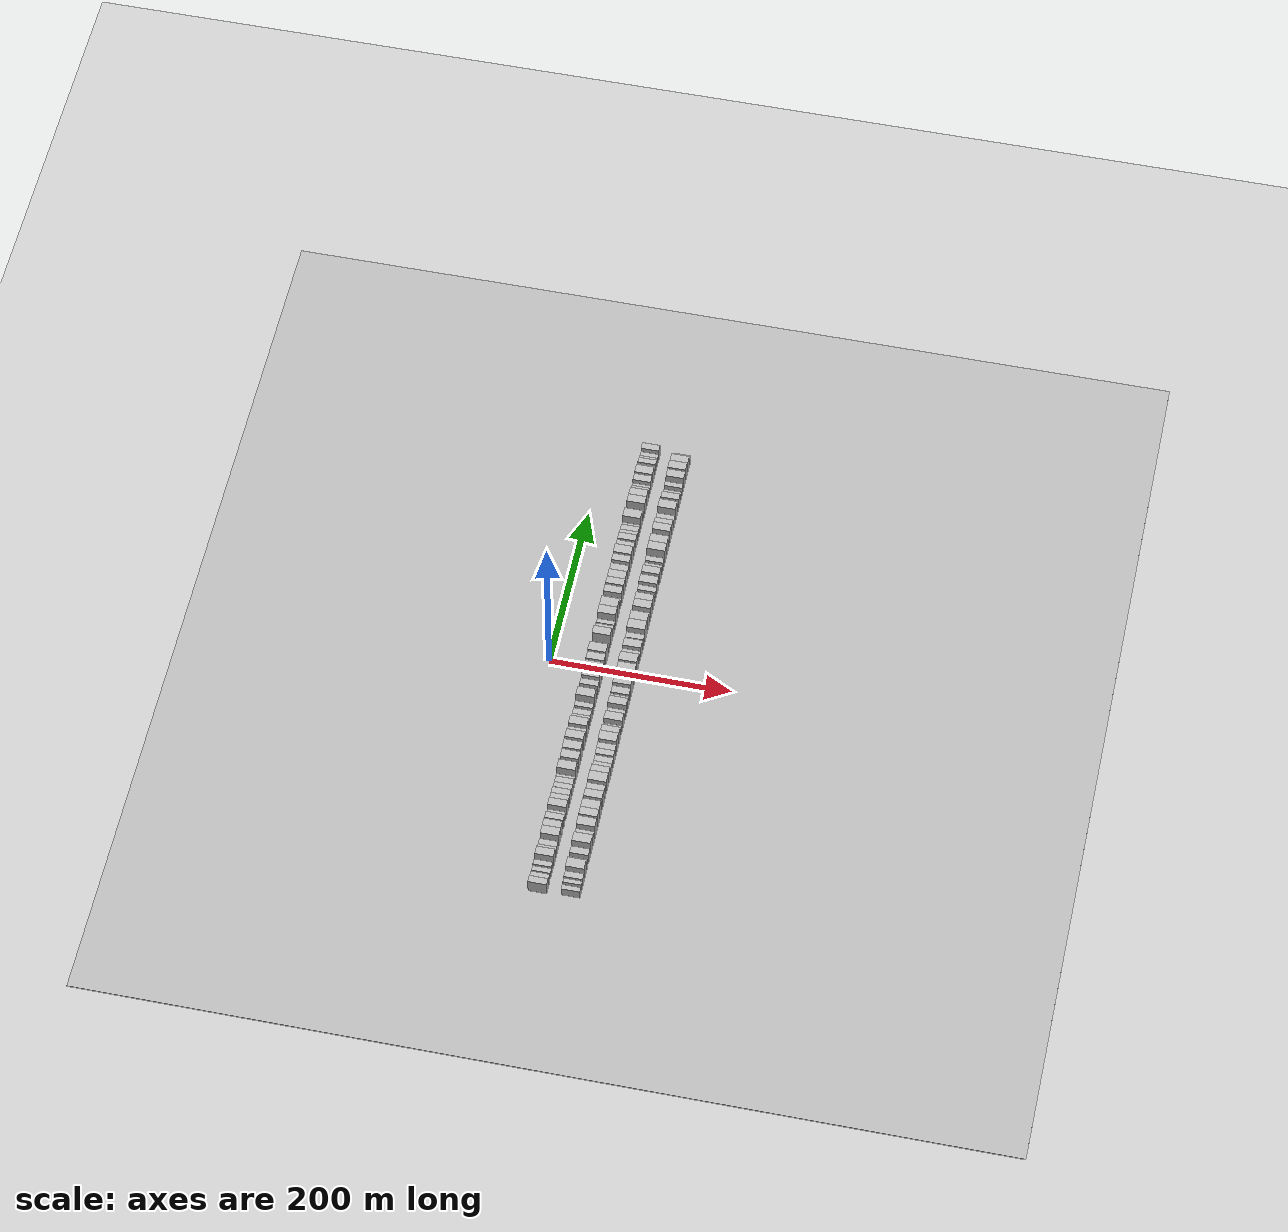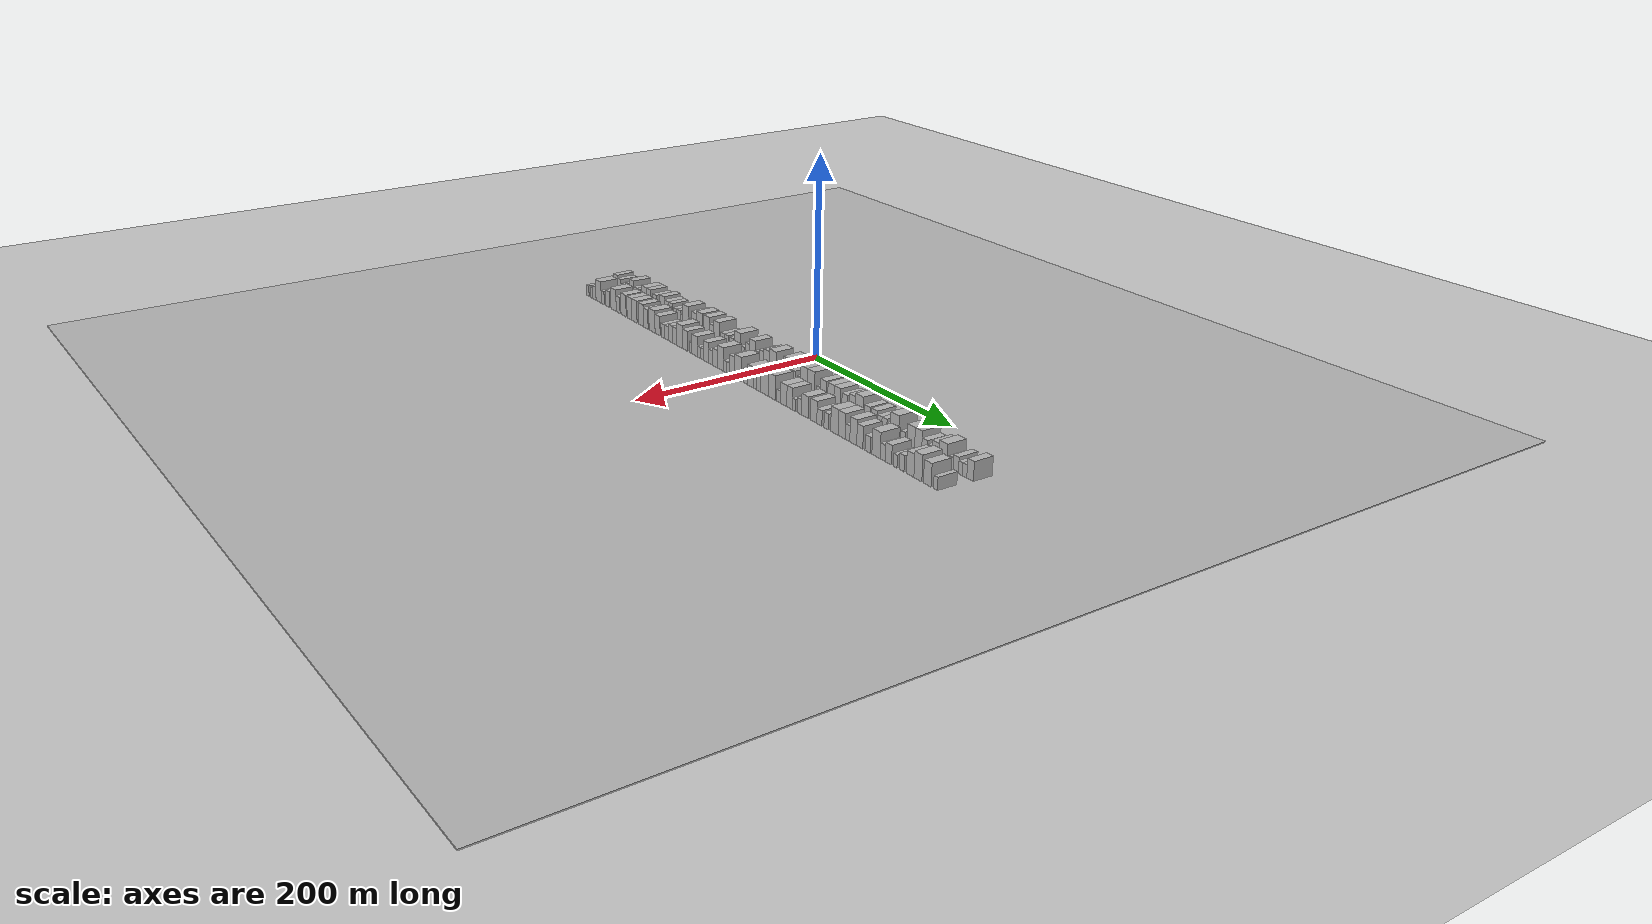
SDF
<?xml version="1.0" encoding="utf-8"?>

<sdf version="1.6">

   <world name="default">

      <gui fullscreen="0">

         <camera name="user_camera">

            <pose>-15 0 4.57585 0 0 0</pose>

            <view_controller>orbit</view_controller>

         </camera>

      </gui>

      <scene>

         <sky>

           <clouds>

             <speed>12</speed>

           </clouds>

         </sky>

         <ambient>0.4 0.4 0.4 1</ambient>

         <background>0.7 0.7 0.7 1</background>

         <shadows>1</shadows>

      </scene>

      <gravity>0 0 -9.8066</gravity>

      <magnetic_field>6e-06 2.3e-05 -4.2e-05</magnetic_field>

      <physics default="0" name="default_physics" type="ode">

         <ode>

            <solver>

               <type>quick</type>

               <iters>10</iters>

               <sor>1.0</sor>

               <use_dynamic_moi_rescaling>0</use_dynamic_moi_rescaling>

            </solver>

            <constraints>

               <cfm>0</cfm>

               <erp>0.2</erp>

               <contact_max_correcting_vel>100</contact_max_correcting_vel>

               <contact_surface_layer>0.001</contact_surface_layer>

            </constraints>

         </ode>

         <max_step_size>0.004</max_step_size>

         <real_time_factor>1</real_time_factor>

         <real_time_update_rate>250</real_time_update_rate>

      </physics>

      <light name="sun" type="directional">

         <cast_shadows>1</cast_shadows>

         <pose>0 0 10 0 0 0</pose>

         <diffuse>0.8 0.8 0.8 1</diffuse>

         <specular>0.2 0.2 0.2 1</specular>

         <attenuation>

            <range>1000</range>

            <constant>0.9</constant>

            <linear>0.01</linear>

            <quadratic>0.001</quadratic>

         </attenuation>

         <direction>-0.5 0.1 -0.9</direction>

      </light>

      <include>

         <name>ground_plane_1</name>

         <uri>model://HANNAS_ground_plane</uri>

         <pose>0 0 0  0 0 0</pose>

      </include>

      <include>

         <name>ground_plane_2</name>

         <uri>model://HANNAS_ground_plane</uri>

         <pose>100 0 0  0 0 0</pose>

      </include>

      <model name="building_1">

         <static>1</static>

         <pose frame="">50.0000 -286.0675 0 0.000000 0.000000 0.000000</pose>

         <link name="link">

            <pose frame="">0 0 9.00 0 0 0</pose>

            <collision name="collision">

               <geometry>

                  <box>

                     <size>20.0000 7.8650 18.0000</size>

                  </box>

               </geometry>

               <max_contacts>10</max_contacts>

               <surface>

                  <contact>

                     <ode/>

                  </contact>

                  <bounce/>

                  <friction>

                     <torsional>

                        <ode/>

                     </torsional>

                     <ode/>

                  </friction>

               </surface>

            </collision>

            <visual name="visual">

               <cast_shadows>0</cast_shadows>

               <geometry>

                  <box>

                     <size>20.0000 7.8650 18.0000</size>

                  </box>

               </geometry>

               <material>

                  <script>

                     <uri>model://HANNAS_wall/materials/scripts</uri>

                     <uri>model://HANNAS_wall/materials/textures</uri>

                     <name>vrc/HANNAS_wall</name>

                  </script>

               </material>

            </visual>

            <self_collide>0</self_collide>

            <enable_wind>0</enable_wind>

            <kinematic>0</kinematic>

         </link>

      </model>

      <model name="building_2">

         <static>1</static>

         <pose frame="">50.0000 -278.4291 0 0.000000 0.000000 0.000000</pose>

         <link name="link">

            <pose frame="">0 0 7.50 0 0 0</pose>

            <collision name="collision">

               <geometry>

                  <box>

                     <size>20.0000 7.4119 15.0000</size>

                  </box>

               </geometry>

               <max_contacts>10</max_contacts>

               <surface>

                  <contact>

                     <ode/>

                  </contact>

                  <bounce/>

                  <friction>

                     <torsional>

                        <ode/>

                     </torsional>

                     <ode/>

                  </friction>

               </surface>

            </collision>

            <visual name="visual">

               <cast_shadows>0</cast_shadows>

               <geometry>

                  <box>

                     <size>20.0000 7.4119 15.0000</size>

                  </box>

               </geometry>

               <material>

                  <script>

                     <uri>model://HANNAS_wall/materials/scripts</uri>

                     <uri>model://HANNAS_wall/materials/textures</uri>

                     <name>vrc/HANNAS_wall</name>

                  </script>

               </material>

            </visual>

            <self_collide>0</self_collide>

            <enable_wind>0</enable_wind>

            <kinematic>0</kinematic>

         </link>

      </model>

      <model name="building_3">

         <static>1</static>

         <pose frame="">50.0000 -268.7812 0 0.000000 0.000000 0.000000</pose>

         <link name="link">

            <pose frame="">0 0 6.00 0 0 0</pose>

            <collision name="collision">

               <geometry>

                  <box>

                     <size>20.0000 5.8838 12.0000</size>

                  </box>

               </geometry>

               <max_contacts>10</max_contacts>

               <surface>

                  <contact>

                     <ode/>

                  </contact>

                  <bounce/>

                  <friction>

                     <torsional>

                        <ode/>

                     </torsional>

                     <ode/>

                  </friction>

               </surface>

            </collision>

            <visual name="visual">

               <cast_shadows>0</cast_shadows>

               <geometry>

                  <box>

                     <size>20.0000 5.8838 12.0000</size>

                  </box>

               </geometry>

               <material>

                  <script>

                     <uri>model://HANNAS_wall/materials/scripts</uri>

                     <uri>model://HANNAS_wall/materials/textures</uri>

                     <name>vrc/HANNAS_wall</name>

                  </script>

               </material>

            </visual>

            <self_collide>0</self_collide>

            <enable_wind>0</enable_wind>

            <kinematic>0</kinematic>

         </link>

      </model>

      <model name="building_4">

         <static>1</static>

         <pose frame="">50.0000 -262.6302 0 0.000000 0.000000 0.000000</pose>

         <link name="link">

            <pose frame="">0 0 7.50 0 0 0</pose>

            <collision name="collision">

               <geometry>

                  <box>

                     <size>20.0000 6.4182 15.0000</size>

                  </box>

               </geometry>

               <max_contacts>10</max_contacts>

               <surface>

                  <contact>

                     <ode/>

                  </contact>

                  <bounce/>

                  <friction>

                     <torsional>

                        <ode/>

                     </torsional>

                     <ode/>

                  </friction>

               </surface>

            </collision>

            <visual name="visual">

               <cast_shadows>0</cast_shadows>

               <geometry>

                  <box>

                     <size>20.0000 6.4182 15.0000</size>

                  </box>

               </geometry>

               <material>

                  <script>

                     <uri>model://HANNAS_wall/materials/scripts</uri>

                     <uri>model://HANNAS_wall/materials/textures</uri>

                     <name>vrc/HANNAS_wall</name>

                  </script>

               </material>

            </visual>

            <self_collide>0</self_collide>

            <enable_wind>0</enable_wind>

            <kinematic>0</kinematic>

         </link>

      </model>

      <model name="building_5">

         <static>1</static>

         <pose frame="">50.0000 -251.6688 0 0.000000 0.000000 0.000000</pose>

         <link name="link">

            <pose frame="">0 0 10.50 0 0 0</pose>

            <collision name="collision">

               <geometry>

                  <box>

                     <size>20.0000 9.5047 21.0000</size>

                  </box>

               </geometry>

               <max_contacts>10</max_contacts>

               <surface>

                  <contact>

                     <ode/>

                  </contact>

                  <bounce/>

                  <friction>

                     <torsional>

                        <ode/>

                     </torsional>

                     <ode/>

                  </friction>

               </surface>

            </collision>

            <visual name="visual">

               <cast_shadows>0</cast_shadows>

               <geometry>

                  <box>

                     <size>20.0000 9.5047 21.0000</size>

                  </box>

               </geometry>

               <material>

                  <script>

                     <uri>model://HANNAS_wall/materials/scripts</uri>

                     <uri>model://HANNAS_wall/materials/textures</uri>

                     <name>vrc/HANNAS_wall</name>

                  </script>

               </material>

            </visual>

            <self_collide>0</self_collide>

            <enable_wind>0</enable_wind>

            <kinematic>0</kinematic>

         </link>

      </model>

      <model name="building_6">

         <static>1</static>

         <pose frame="">50.0000 -243.5959 0 0.000000 0.000000 0.000000</pose>

         <link name="link">

            <pose frame="">0 0 7.50 0 0 0</pose>

            <collision name="collision">

               <geometry>

                  <box>

                     <size>20.0000 6.6412 15.0000</size>

                  </box>

               </geometry>

               <max_contacts>10</max_contacts>

               <surface>

                  <contact>

                     <ode/>

                  </contact>

                  <bounce/>

                  <friction>

                     <torsional>

                        <ode/>

                     </torsional>

                     <ode/>

                  </friction>

               </surface>

            </collision>

            <visual name="visual">

               <cast_shadows>0</cast_shadows>

               <geometry>

                  <box>

                     <size>20.0000 6.6412 15.0000</size>

                  </box>

               </geometry>

               <material>

                  <script>

                     <uri>model://HANNAS_wall/materials/scripts</uri>

                     <uri>model://HANNAS_wall/materials/textures</uri>

                     <name>vrc/HANNAS_wall</name>

                  </script>

               </material>

            </visual>

            <self_collide>0</self_collide>

            <enable_wind>0</enable_wind>

            <kinematic>0</kinematic>

         </link>

      </model>

      <model name="building_7">

         <static>1</static>

         <pose frame="">50.0000 -236.7432 0 0.000000 0.000000 0.000000</pose>

         <link name="link">

            <pose frame="">0 0 7.50 0 0 0</pose>

            <collision name="collision">

               <geometry>

                  <box>

                     <size>20.0000 7.0642 15.0000</size>

                  </box>

               </geometry>

               <max_contacts>10</max_contacts>

               <surface>

                  <contact>

                     <ode/>

                  </contact>

                  <bounce/>

                  <friction>

                     <torsional>

                        <ode/>

                     </torsional>

                     <ode/>

                  </friction>

               </surface>

            </collision>

            <visual name="visual">

               <cast_shadows>0</cast_shadows>

               <geometry>

                  <box>

                     <size>20.0000 7.0642 15.0000</size>

                  </box>

               </geometry>

               <material>

                  <script>

                     <uri>model://HANNAS_wall/materials/scripts</uri>

                     <uri>model://HANNAS_wall/materials/textures</uri>

                     <name>vrc/HANNAS_wall</name>

                  </script>

               </material>

            </visual>

            <self_collide>0</self_collide>

            <enable_wind>0</enable_wind>

            <kinematic>0</kinematic>

         </link>

      </model>

      <model name="building_8">

         <static>1</static>

         <pose frame="">50.0000 -225.0730 0 0.000000 0.000000 0.000000</pose>

         <link name="link">

            <pose frame="">0 0 10.50 0 0 0</pose>

            <collision name="collision">

               <geometry>

                  <box>

                     <size>20.0000 10.2760 21.0000</size>

                  </box>

               </geometry>

               <max_contacts>10</max_contacts>

               <surface>

                  <contact>

                     <ode/>

                  </contact>

                  <bounce/>

                  <friction>

                     <torsional>

                        <ode/>

                     </torsional>

                     <ode/>

                  </friction>

               </surface>

            </collision>

            <visual name="visual">

               <cast_shadows>0</cast_shadows>

               <geometry>

                  <box>

                     <size>20.0000 10.2760 21.0000</size>

                  </box>

               </geometry>

               <material>

                  <script>

                     <uri>model://HANNAS_wall/materials/scripts</uri>

                     <uri>model://HANNAS_wall/materials/textures</uri>

                     <name>vrc/HANNAS_wall</name>

                  </script>

               </material>

            </visual>

            <self_collide>0</self_collide>

            <enable_wind>0</enable_wind>

            <kinematic>0</kinematic>

         </link>

      </model>

      <model name="building_9">

         <static>1</static>

         <pose frame="">50.0000 -215.6762 0 0.000000 0.000000 0.000000</pose>

         <link name="link">

            <pose frame="">0 0 10.50 0 0 0</pose>

            <collision name="collision">

               <geometry>

                  <box>

                     <size>20.0000 8.5176 21.0000</size>

                  </box>

               </geometry>

               <max_contacts>10</max_contacts>

               <surface>

                  <contact>

                     <ode/>

                  </contact>

                  <bounce/>

                  <friction>

                     <torsional>

                        <ode/>

                     </torsional>

                     <ode/>

                  </friction>

               </surface>

            </collision>

            <visual name="visual">

               <cast_shadows>0</cast_shadows>

               <geometry>

                  <box>

                     <size>20.0000 8.5176 21.0000</size>

                  </box>

               </geometry>

               <material>

                  <script>

                     <uri>model://HANNAS_wall/materials/scripts</uri>

                     <uri>model://HANNAS_wall/materials/textures</uri>

                     <name>vrc/HANNAS_wall</name>

                  </script>

               </material>

            </visual>

            <self_collide>0</self_collide>

            <enable_wind>0</enable_wind>

            <kinematic>0</kinematic>

         </link>

      </model>

      <model name="building_10">

         <static>1</static>

         <pose frame="">50.0000 -204.5940 0 0.000000 0.000000 0.000000</pose>

         <link name="link">

            <pose frame="">0 0 9.00 0 0 0</pose>

            <collision name="collision">

               <geometry>

                  <box>

                     <size>20.0000 7.6467 18.0000</size>

                  </box>

               </geometry>

               <max_contacts>10</max_contacts>

               <surface>

                  <contact>

                     <ode/>

                  </contact>

                  <bounce/>

                  <friction>

                     <torsional>

                        <ode/>

                     </torsional>

                     <ode/>

                  </friction>

               </surface>

            </collision>

            <visual name="visual">

               <cast_shadows>0</cast_shadows>

               <geometry>

                  <box>

                     <size>20.0000 7.6467 18.0000</size>

                  </box>

               </geometry>

               <material>

                  <script>

                     <uri>model://HANNAS_wall/materials/scripts</uri>

                     <uri>model://HANNAS_wall/materials/textures</uri>

                     <name>vrc/HANNAS_wall</name>

                  </script>

               </material>

            </visual>

            <self_collide>0</self_collide>

            <enable_wind>0</enable_wind>

            <kinematic>0</kinematic>

         </link>

      </model>

      <model name="building_11">

         <static>1</static>

         <pose frame="">50.0000 -196.3125 0 0.000000 0.000000 0.000000</pose>

         <link name="link">

            <pose frame="">0 0 6.00 0 0 0</pose>

            <collision name="collision">

               <geometry>

                  <box>

                     <size>20.0000 4.9163 12.0000</size>

                  </box>

               </geometry>

               <max_contacts>10</max_contacts>

               <surface>

                  <contact>

                     <ode/>

                  </contact>

                  <bounce/>

                  <friction>

                     <torsional>

                        <ode/>

                     </torsional>

                     <ode/>

                  </friction>

               </surface>

            </collision>

            <visual name="visual">

               <cast_shadows>0</cast_shadows>

               <geometry>

                  <box>

                     <size>20.0000 4.9163 12.0000</size>

                  </box>

               </geometry>

               <material>

                  <script>

                     <uri>model://HANNAS_wall/materials/scripts</uri>

                     <uri>model://HANNAS_wall/materials/textures</uri>

                     <name>vrc/HANNAS_wall</name>

                  </script>

               </material>

            </visual>

            <self_collide>0</self_collide>

            <enable_wind>0</enable_wind>

            <kinematic>0</kinematic>

         </link>

      </model>

      <model name="building_12">

         <static>1</static>

         <pose frame="">50.0000 -189.1845 0 0.000000 0.000000 0.000000</pose>

         <link name="link">

            <pose frame="">0 0 10.50 0 0 0</pose>

            <collision name="collision">

               <geometry>

                  <box>

                     <size>20.0000 9.3396 21.0000</size>

                  </box>

               </geometry>

               <max_contacts>10</max_contacts>

               <surface>

                  <contact>

                     <ode/>

                  </contact>

                  <bounce/>

                  <friction>

                     <torsional>

                        <ode/>

                     </torsional>

                     <ode/>

                  </friction>

               </surface>

            </collision>

            <visual name="visual">

               <cast_shadows>0</cast_shadows>

               <geometry>

                  <box>

                     <size>20.0000 9.3396 21.0000</size>

                  </box>

               </geometry>

               <material>

                  <script>

                     <uri>model://HANNAS_wall/materials/scripts</uri>

                     <uri>model://HANNAS_wall/materials/textures</uri>

                     <name>vrc/HANNAS_wall</name>

                  </script>

               </material>

            </visual>

            <self_collide>0</self_collide>

            <enable_wind>0</enable_wind>

            <kinematic>0</kinematic>

         </link>

      </model>

      <model name="building_13">

         <static>1</static>

         <pose frame="">50.0000 -180.3806 0 0.000000 0.000000 0.000000</pose>

         <link name="link">

            <pose frame="">0 0 9.00 0 0 0</pose>

            <collision name="collision">

               <geometry>

                  <box>

                     <size>20.0000 8.2682 18.0000</size>

                  </box>

               </geometry>

               <max_contacts>10</max_contacts>

               <surface>

                  <contact>

                     <ode/>

                  </contact>

                  <bounce/>

                  <friction>

                     <torsional>

                        <ode/>

                     </torsional>

                     <ode/>

                  </friction>

               </surface>

            </collision>

            <visual name="visual">

               <cast_shadows>0</cast_shadows>

               <geometry>

                  <box>

                     <size>20.0000 8.2682 18.0000</size>

                  </box>

               </geometry>

               <material>

                  <script>

                     <uri>model://HANNAS_wall/materials/scripts</uri>

                     <uri>model://HANNAS_wall/materials/textures</uri>

                     <name>vrc/HANNAS_wall</name>

                  </script>

               </material>

            </visual>

            <self_collide>0</self_collide>

            <enable_wind>0</enable_wind>

            <kinematic>0</kinematic>

         </link>

      </model>

      <model name="building_14">

         <static>1</static>

         <pose frame="">50.0000 -172.5509 0 0.000000 0.000000 0.000000</pose>

         <link name="link">

            <pose frame="">0 0 9.00 0 0 0</pose>

            <collision name="collision">

               <geometry>

                  <box>

                     <size>20.0000 7.3913 18.0000</size>

                  </box>

               </geometry>

               <max_contacts>10</max_contacts>

               <surface>

                  <contact>

                     <ode/>

                  </contact>

                  <bounce/>

                  <friction>

                     <torsional>

                        <ode/>

                     </torsional>

                     <ode/>

                  </friction>

               </surface>

            </collision>

            <visual name="visual">

               <cast_shadows>0</cast_shadows>

               <geometry>

                  <box>

                     <size>20.0000 7.3913 18.0000</size>

                  </box>

               </geometry>

               <material>

                  <script>

                     <uri>model://HANNAS_wall/materials/scripts</uri>

                     <uri>model://HANNAS_wall/materials/textures</uri>

                     <name>vrc/HANNAS_wall</name>

                  </script>

               </material>

            </visual>

            <self_collide>0</self_collide>

            <enable_wind>0</enable_wind>

            <kinematic>0</kinematic>

         </link>

      </model>

      <model name="building_15">

         <static>1</static>

         <pose frame="">50.0000 -163.5788 0 0.000000 0.000000 0.000000</pose>

         <link name="link">

            <pose frame="">0 0 7.50 0 0 0</pose>

            <collision name="collision">

               <geometry>

                  <box>

                     <size>20.0000 6.5529 15.0000</size>

                  </box>

               </geometry>

               <max_contacts>10</max_contacts>

               <surface>

                  <contact>

                     <ode/>

                  </contact>

                  <bounce/>

                  <friction>

                     <torsional>

                        <ode/>

                     </torsional>

                     <ode/>

                  </friction>

               </surface>

            </collision>

            <visual name="visual">

               <cast_shadows>0</cast_shadows>

               <geometry>

                  <box>

                     <size>20.0000 6.5529 15.0000</size>

                  </box>

               </geometry>

               <material>

                  <script>

                     <uri>model://HANNAS_wall/materials/scripts</uri>

                     <uri>model://HANNAS_wall/materials/textures</uri>

                     <name>vrc/HANNAS_wall</name>

                  </script>

               </material>

            </visual>

            <self_collide>0</self_collide>

            <enable_wind>0</enable_wind>

            <kinematic>0</kinematic>

         </link>

      </model>

      <model name="building_16">

         <static>1</static>

         <pose frame="">50.0000 -156.7487 0 0.000000 0.000000 0.000000</pose>

         <link name="link">

            <pose frame="">0 0 7.50 0 0 0</pose>

            <collision name="collision">

               <geometry>

                  <box>

                     <size>20.0000 7.1074 15.0000</size>

                  </box>

               </geometry>

               <max_contacts>10</max_contacts>

               <surface>

                  <contact>

                     <ode/>

                  </contact>

                  <bounce/>

                  <friction>

                     <torsional>

                        <ode/>

                     </torsional>

                     <ode/>

                  </friction>

               </surface>

            </collision>

            <visual name="visual">

               <cast_shadows>0</cast_shadows>

               <geometry>

                  <box>

                     <size>20.0000 7.1074 15.0000</size>

                  </box>

               </geometry>

               <material>

                  <script>

                     <uri>model://HANNAS_wall/materials/scripts</uri>

                     <uri>model://HANNAS_wall/materials/textures</uri>

                     <name>vrc/HANNAS_wall</name>

                  </script>

               </material>

            </visual>

            <self_collide>0</self_collide>

            <enable_wind>0</enable_wind>

            <kinematic>0</kinematic>

         </link>

      </model>

      <model name="building_17">

         <static>1</static>

         <pose frame="">50.0000 -150.6562 0 0.000000 0.000000 0.000000</pose>

         <link name="link">

            <pose frame="">0 0 6.00 0 0 0</pose>

            <collision name="collision">

               <geometry>

                  <box>

                     <size>20.0000 5.0775 12.0000</size>

                  </box>

               </geometry>

               <max_contacts>10</max_contacts>

               <surface>

                  <contact>

                     <ode/>

                  </contact>

                  <bounce/>

                  <friction>

                     <torsional>

                        <ode/>

                     </torsional>

                     <ode/>

                  </friction>

               </surface>

            </collision>

            <visual name="visual">

               <cast_shadows>0</cast_shadows>

               <geometry>

                  <box>

                     <size>20.0000 5.0775 12.0000</size>

                  </box>

               </geometry>

               <material>

                  <script>

                     <uri>model://HANNAS_wall/materials/scripts</uri>

                     <uri>model://HANNAS_wall/materials/textures</uri>

                     <name>vrc/HANNAS_wall</name>

                  </script>

               </material>

            </visual>

            <self_collide>0</self_collide>

            <enable_wind>0</enable_wind>

            <kinematic>0</kinematic>

         </link>

      </model>

      <model name="building_18">

         <static>1</static>

         <pose frame="">50.0000 -142.7013 0 0.000000 0.000000 0.000000</pose>

         <link name="link">

            <pose frame="">0 0 12.00 0 0 0</pose>

            <collision name="collision">

               <geometry>

                  <box>

                     <size>20.0000 10.8324 24.0000</size>

                  </box>

               </geometry>

               <max_contacts>10</max_contacts>

               <surface>

                  <contact>

                     <ode/>

                  </contact>

                  <bounce/>

                  <friction>

                     <torsional>

                        <ode/>

                     </torsional>

                     <ode/>

                  </friction>

               </surface>

            </collision>

            <visual name="visual">

               <cast_shadows>0</cast_shadows>

               <geometry>

                  <box>

                     <size>20.0000 10.8324 24.0000</size>

                  </box>

               </geometry>

               <material>

                  <script>

                     <uri>model://HANNAS_wall/materials/scripts</uri>

                     <uri>model://HANNAS_wall/materials/textures</uri>

                     <name>vrc/HANNAS_wall</name>

                  </script>

               </material>

            </visual>

            <self_collide>0</self_collide>

            <enable_wind>0</enable_wind>

            <kinematic>0</kinematic>

         </link>

      </model>

      <model name="building_19">

         <static>1</static>

         <pose frame="">50.0000 -134.6364 0 0.000000 0.000000 0.000000</pose>

         <link name="link">

            <pose frame="">0 0 6.00 0 0 0</pose>

            <collision name="collision">

               <geometry>

                  <box>

                     <size>20.0000 5.2974 12.0000</size>

                  </box>

               </geometry>

               <max_contacts>10</max_contacts>

               <surface>

                  <contact>

                     <ode/>

                  </contact>

                  <bounce/>

                  <friction>

                     <torsional>

                        <ode/>

                     </torsional>

                     <ode/>

                  </friction>

               </surface>

            </collision>

            <visual name="visual">

               <cast_shadows>0</cast_shadows>

               <geometry>

                  <box>

                     <size>20.0000 5.2974 12.0000</size>

                  </box>

               </geometry>

               <material>

                  <script>

                     <uri>model://HANNAS_wall/materials/scripts</uri>

                     <uri>model://HANNAS_wall/materials/textures</uri>

                     <name>vrc/HANNAS_wall</name>

                  </script>

               </material>

            </visual>

            <self_collide>0</self_collide>

            <enable_wind>0</enable_wind>

            <kinematic>0</kinematic>

         </link>

      </model>

      <model name="building_20">

         <static>1</static>

         <pose frame="">50.0000 -126.8587 0 0.000000 0.000000 0.000000</pose>

         <link name="link">

            <pose frame="">0 0 10.50 0 0 0</pose>

            <collision name="collision">

               <geometry>

                  <box>

                     <size>20.0000 10.2580 21.0000</size>

                  </box>

               </geometry>

               <max_contacts>10</max_contacts>

               <surface>

                  <contact>

                     <ode/>

                  </contact>

                  <bounce/>

                  <friction>

                     <torsional>

                        <ode/>

                     </torsional>

                     <ode/>

                  </friction>

               </surface>

            </collision>

            <visual name="visual">

               <cast_shadows>0</cast_shadows>

               <geometry>

                  <box>

                     <size>20.0000 10.2580 21.0000</size>

                  </box>

               </geometry>

               <material>

                  <script>

                     <uri>model://HANNAS_wall/materials/scripts</uri>

                     <uri>model://HANNAS_wall/materials/textures</uri>

                     <name>vrc/HANNAS_wall</name>

                  </script>

               </material>

            </visual>

            <self_collide>0</self_collide>

            <enable_wind>0</enable_wind>

            <kinematic>0</kinematic>

         </link>

      </model>

      <model name="building_21">

         <static>1</static>

         <pose frame="">50.0000 -116.3486 0 0.000000 0.000000 0.000000</pose>

         <link name="link">

            <pose frame="">0 0 12.00 0 0 0</pose>

            <collision name="collision">

               <geometry>

                  <box>

                     <size>20.0000 10.7622 24.0000</size>

                  </box>

               </geometry>

               <max_contacts>10</max_contacts>

               <surface>

                  <contact>

                     <ode/>

                  </contact>

                  <bounce/>

                  <friction>

                     <torsional>

                        <ode/>

                     </torsional>

                     <ode/>

                  </friction>

               </surface>

            </collision>

            <visual name="visual">

               <cast_shadows>0</cast_shadows>

               <geometry>

                  <box>

                     <size>20.0000 10.7622 24.0000</size>

                  </box>

               </geometry>

               <material>

                  <script>

                     <uri>model://HANNAS_wall/materials/scripts</uri>

                     <uri>model://HANNAS_wall/materials/textures</uri>

                     <name>vrc/HANNAS_wall</name>

                  </script>

               </material>

            </visual>

            <self_collide>0</self_collide>

            <enable_wind>0</enable_wind>

            <kinematic>0</kinematic>

         </link>

      </model>

      <model name="building_22">

         <static>1</static>

         <pose frame="">50.0000 -102.8429 0 0.000000 0.000000 0.000000</pose>

         <link name="link">

            <pose frame="">0 0 12.00 0 0 0</pose>

            <collision name="collision">

               <geometry>

                  <box>

                     <size>20.0000 10.2493 24.0000</size>

                  </box>

               </geometry>

               <max_contacts>10</max_contacts>

               <surface>

                  <contact>

                     <ode/>

                  </contact>

                  <bounce/>

                  <friction>

                     <torsional>

                        <ode/>

                     </torsional>

                     <ode/>

                  </friction>

               </surface>

            </collision>

            <visual name="visual">

               <cast_shadows>0</cast_shadows>

               <geometry>

                  <box>

                     <size>20.0000 10.2493 24.0000</size>

                  </box>

               </geometry>

               <material>

                  <script>

                     <uri>model://HANNAS_wall/materials/scripts</uri>

                     <uri>model://HANNAS_wall/materials/textures</uri>

                     <name>vrc/HANNAS_wall</name>

                  </script>

               </material>

            </visual>

            <self_collide>0</self_collide>

            <enable_wind>0</enable_wind>

            <kinematic>0</kinematic>

         </link>

      </model>

      <model name="building_23">

         <static>1</static>

         <pose frame="">50.0000 -93.9561 0 0.000000 0.000000 0.000000</pose>

         <link name="link">

            <pose frame="">0 0 9.00 0 0 0</pose>

            <collision name="collision">

               <geometry>

                  <box>

                     <size>20.0000 7.5243 18.0000</size>

                  </box>

               </geometry>

               <max_contacts>10</max_contacts>

               <surface>

                  <contact>

                     <ode/>

                  </contact>

                  <bounce/>

                  <friction>

                     <torsional>

                        <ode/>

                     </torsional>

                     <ode/>

                  </friction>

               </surface>

            </collision>

            <visual name="visual">

               <cast_shadows>0</cast_shadows>

               <geometry>

                  <box>

                     <size>20.0000 7.5243 18.0000</size>

                  </box>

               </geometry>

               <material>

                  <script>

                     <uri>model://HANNAS_wall/materials/scripts</uri>

                     <uri>model://HANNAS_wall/materials/textures</uri>

                     <name>vrc/HANNAS_wall</name>

                  </script>

               </material>

            </visual>

            <self_collide>0</self_collide>

            <enable_wind>0</enable_wind>

            <kinematic>0</kinematic>

         </link>

      </model>

      <model name="building_24">

         <static>1</static>

         <pose frame="">50.0000 -85.1088 0 0.000000 0.000000 0.000000</pose>

         <link name="link">

            <pose frame="">0 0 12.00 0 0 0</pose>

            <collision name="collision">

               <geometry>

                  <box>

                     <size>20.0000 10.1702 24.0000</size>

                  </box>

               </geometry>

               <max_contacts>10</max_contacts>

               <surface>

                  <contact>

                     <ode/>

                  </contact>

                  <bounce/>

                  <friction>

                     <torsional>

                        <ode/>

                     </torsional>

                     <ode/>

                  </friction>

               </surface>

            </collision>

            <visual name="visual">

               <cast_shadows>0</cast_shadows>

               <geometry>

                  <box>

                     <size>20.0000 10.1702 24.0000</size>

                  </box>

               </geometry>

               <material>

                  <script>

                     <uri>model://HANNAS_wall/materials/scripts</uri>

                     <uri>model://HANNAS_wall/materials/textures</uri>

                     <name>vrc/HANNAS_wall</name>

                  </script>

               </material>

            </visual>

            <self_collide>0</self_collide>

            <enable_wind>0</enable_wind>

            <kinematic>0</kinematic>

         </link>

      </model>

      <model name="building_25">

         <static>1</static>

         <pose frame="">50.0000 -74.5990 0 0.000000 0.000000 0.000000</pose>

         <link name="link">

            <pose frame="">0 0 7.50 0 0 0</pose>

            <collision name="collision">

               <geometry>

                  <box>

                     <size>20.0000 6.8495 15.0000</size>

                  </box>

               </geometry>

               <max_contacts>10</max_contacts>

               <surface>

                  <contact>

                     <ode/>

                  </contact>

                  <bounce/>

                  <friction>

                     <torsional>

                        <ode/>

                     </torsional>

                     <ode/>

                  </friction>

               </surface>

            </collision>

            <visual name="visual">

               <cast_shadows>0</cast_shadows>

               <geometry>

                  <box>

                     <size>20.0000 6.8495 15.0000</size>

                  </box>

               </geometry>

               <material>

                  <script>

                     <uri>model://HANNAS_wall/materials/scripts</uri>

                     <uri>model://HANNAS_wall/materials/textures</uri>

                     <name>vrc/HANNAS_wall</name>

                  </script>

               </material>

            </visual>

            <self_collide>0</self_collide>

            <enable_wind>0</enable_wind>

            <kinematic>0</kinematic>

         </link>

      </model>

      <model name="building_26">

         <static>1</static>

         <pose frame="">50.0000 -67.6113 0 0.000000 0.000000 0.000000</pose>

         <link name="link">

            <pose frame="">0 0 7.50 0 0 0</pose>

            <collision name="collision">

               <geometry>

                  <box>

                     <size>20.0000 7.1259 15.0000</size>

                  </box>

               </geometry>

               <max_contacts>10</max_contacts>

               <surface>

                  <contact>

                     <ode/>

                  </contact>

                  <bounce/>

                  <friction>

                     <torsional>

                        <ode/>

                     </torsional>

                     <ode/>

                  </friction>

               </surface>

            </collision>

            <visual name="visual">

               <cast_shadows>0</cast_shadows>

               <geometry>

                  <box>

                     <size>20.0000 7.1259 15.0000</size>

                  </box>

               </geometry>

               <material>

                  <script>

                     <uri>model://HANNAS_wall/materials/scripts</uri>

                     <uri>model://HANNAS_wall/materials/textures</uri>

                     <name>vrc/HANNAS_wall</name>

                  </script>

               </material>

            </visual>

            <self_collide>0</self_collide>

            <enable_wind>0</enable_wind>

            <kinematic>0</kinematic>

         </link>

      </model>

      <model name="building_27">

         <static>1</static>

         <pose frame="">50.0000 -57.8400 0 0.000000 0.000000 0.000000</pose>

         <link name="link">

            <pose frame="">0 0 7.50 0 0 0</pose>

            <collision name="collision">

               <geometry>

                  <box>

                     <size>20.0000 6.4167 15.0000</size>

                  </box>

               </geometry>

               <max_contacts>10</max_contacts>

               <surface>

                  <contact>

                     <ode/>

                  </contact>

                  <bounce/>

                  <friction>

                     <torsional>

                        <ode/>

                     </torsional>

                     <ode/>

                  </friction>

               </surface>

            </collision>

            <visual name="visual">

               <cast_shadows>0</cast_shadows>

               <geometry>

                  <box>

                     <size>20.0000 6.4167 15.0000</size>

                  </box>

               </geometry>

               <material>

                  <script>

                     <uri>model://HANNAS_wall/materials/scripts</uri>

                     <uri>model://HANNAS_wall/materials/textures</uri>

                     <name>vrc/HANNAS_wall</name>

                  </script>

               </material>

            </visual>

            <self_collide>0</self_collide>

            <enable_wind>0</enable_wind>

            <kinematic>0</kinematic>

         </link>

      </model>

      <model name="building_28">

         <static>1</static>

         <pose frame="">50.0000 -47.2532 0 0.000000 0.000000 0.000000</pose>

         <link name="link">

            <pose frame="">0 0 12.00 0 0 0</pose>

            <collision name="collision">

               <geometry>

                  <box>

                     <size>20.0000 10.7568 24.0000</size>

                  </box>

               </geometry>

               <max_contacts>10</max_contacts>

               <surface>

                  <contact>

                     <ode/>

                  </contact>

                  <bounce/>

                  <friction>

                     <torsional>

                        <ode/>

                     </torsional>

                     <ode/>

                  </friction>

               </surface>

            </collision>

            <visual name="visual">

               <cast_shadows>0</cast_shadows>

               <geometry>

                  <box>

                     <size>20.0000 10.7568 24.0000</size>

                  </box>

               </geometry>

               <material>

                  <script>

                     <uri>model://HANNAS_wall/materials/scripts</uri>

                     <uri>model://HANNAS_wall/materials/textures</uri>

                     <name>vrc/HANNAS_wall</name>

                  </script>

               </material>

            </visual>

            <self_collide>0</self_collide>

            <enable_wind>0</enable_wind>

            <kinematic>0</kinematic>

         </link>

      </model>

      <model name="building_29">

         <static>1</static>

         <pose frame="">50.0000 -38.8885 0 0.000000 0.000000 0.000000</pose>

         <link name="link">

            <pose frame="">0 0 6.00 0 0 0</pose>

            <collision name="collision">

               <geometry>

                  <box>

                     <size>20.0000 5.9726 12.0000</size>

                  </box>

               </geometry>

               <max_contacts>10</max_contacts>

               <surface>

                  <contact>

                     <ode/>

                  </contact>

                  <bounce/>

                  <friction>

                     <torsional>

                        <ode/>

                     </torsional>

                     <ode/>

                  </friction>

               </surface>

            </collision>

            <visual name="visual">

               <cast_shadows>0</cast_shadows>

               <geometry>

                  <box>

                     <size>20.0000 5.9726 12.0000</size>

                  </box>

               </geometry>

               <material>

                  <script>

                     <uri>model://HANNAS_wall/materials/scripts</uri>

                     <uri>model://HANNAS_wall/materials/textures</uri>

                     <name>vrc/HANNAS_wall</name>

                  </script>

               </material>

            </visual>

            <self_collide>0</self_collide>

            <enable_wind>0</enable_wind>

            <kinematic>0</kinematic>

         </link>

      </model>

      <model name="building_30">

         <static>1</static>

         <pose frame="">50.0000 -30.2129 0 0.000000 0.000000 0.000000</pose>

         <link name="link">

            <pose frame="">0 0 9.00 0 0 0</pose>

            <collision name="collision">

               <geometry>

                  <box>

                     <size>20.0000 7.3786 18.0000</size>

                  </box>

               </geometry>

               <max_contacts>10</max_contacts>

               <surface>

                  <contact>

                     <ode/>

                  </contact>

                  <bounce/>

                  <friction>

                     <torsional>

                        <ode/>

                     </torsional>

                     <ode/>

                  </friction>

               </surface>

            </collision>

            <visual name="visual">

               <cast_shadows>0</cast_shadows>

               <geometry>

                  <box>

                     <size>20.0000 7.3786 18.0000</size>

                  </box>

               </geometry>

               <material>

                  <script>

                     <uri>model://HANNAS_wall/materials/scripts</uri>

                     <uri>model://HANNAS_wall/materials/textures</uri>

                     <name>vrc/HANNAS_wall</name>

                  </script>

               </material>

            </visual>

            <self_collide>0</self_collide>

            <enable_wind>0</enable_wind>

            <kinematic>0</kinematic>

         </link>

      </model>

      <model name="building_31">

         <static>1</static>

         <pose frame="">50.0000 -21.6969 0 0.000000 0.000000 0.000000</pose>

         <link name="link">

            <pose frame="">0 0 12.00 0 0 0</pose>

            <collision name="collision">

               <geometry>

                  <box>

                     <size>20.0000 9.6533 24.0000</size>

                  </box>

               </geometry>

               <max_contacts>10</max_contacts>

               <surface>

                  <contact>

                     <ode/>

                  </contact>

                  <bounce/>

                  <friction>

                     <torsional>

                        <ode/>

                     </torsional>

                     <ode/>

                  </friction>

               </surface>

            </collision>

            <visual name="visual">

               <cast_shadows>0</cast_shadows>

               <geometry>

                  <box>

                     <size>20.0000 9.6533 24.0000</size>

                  </box>

               </geometry>

               <material>

                  <script>

                     <uri>model://HANNAS_wall/materials/scripts</uri>

                     <uri>model://HANNAS_wall/materials/textures</uri>

                     <name>vrc/HANNAS_wall</name>

                  </script>

               </material>

            </visual>

            <self_collide>0</self_collide>

            <enable_wind>0</enable_wind>

            <kinematic>0</kinematic>

         </link>

      </model>

      <model name="building_32">

         <static>1</static>

         <pose frame="">50.0000 -13.5113 0 0.000000 0.000000 0.000000</pose>

         <link name="link">

            <pose frame="">0 0 7.50 0 0 0</pose>

            <collision name="collision">

               <geometry>

                  <box>

                     <size>20.0000 6.7177 15.0000</size>

                  </box>

               </geometry>

               <max_contacts>10</max_contacts>

               <surface>

                  <contact>

                     <ode/>

                  </contact>

                  <bounce/>

                  <friction>

                     <torsional>

                        <ode/>

                     </torsional>

                     <ode/>

                  </friction>

               </surface>

            </collision>

            <visual name="visual">

               <cast_shadows>0</cast_shadows>

               <geometry>

                  <box>

                     <size>20.0000 6.7177 15.0000</size>

                  </box>

               </geometry>

               <material>

                  <script>

                     <uri>model://HANNAS_wall/materials/scripts</uri>

                     <uri>model://HANNAS_wall/materials/textures</uri>

                     <name>vrc/HANNAS_wall</name>

                  </script>

               </material>

            </visual>

            <self_collide>0</self_collide>

            <enable_wind>0</enable_wind>

            <kinematic>0</kinematic>

         </link>

      </model>

      <model name="building_33">

         <static>1</static>

         <pose frame="">50.0000 -6.1777 0 0.000000 0.000000 0.000000</pose>

         <link name="link">

            <pose frame="">0 0 9.00 0 0 0</pose>

            <collision name="collision">

               <geometry>

                  <box>

                     <size>20.0000 7.9495 18.0000</size>

                  </box>

               </geometry>

               <max_contacts>10</max_contacts>

               <surface>

                  <contact>

                     <ode/>

                  </contact>

                  <bounce/>

                  <friction>

                     <torsional>

                        <ode/>

                     </torsional>

                     <ode/>

                  </friction>

               </surface>

            </collision>

            <visual name="visual">

               <cast_shadows>0</cast_shadows>

               <geometry>

                  <box>

                     <size>20.0000 7.9495 18.0000</size>

                  </box>

               </geometry>

               <material>

                  <script>

                     <uri>model://HANNAS_wall/materials/scripts</uri>

                     <uri>model://HANNAS_wall/materials/textures</uri>

                     <name>vrc/HANNAS_wall</name>

                  </script>

               </material>

            </visual>

            <self_collide>0</self_collide>

            <enable_wind>0</enable_wind>

            <kinematic>0</kinematic>

         </link>

      </model>

      <model name="building_34">

         <static>1</static>

         <pose frame="">50.0000 2.4501 0 0.000000 0.000000 0.000000</pose>

         <link name="link">

            <pose frame="">0 0 10.50 0 0 0</pose>

            <collision name="collision">

               <geometry>

                  <box>

                     <size>20.0000 9.3061 21.0000</size>

                  </box>

               </geometry>

               <max_contacts>10</max_contacts>

               <surface>

                  <contact>

                     <ode/>

                  </contact>

                  <bounce/>

                  <friction>

                     <torsional>

                        <ode/>

                     </torsional>

                     <ode/>

                  </friction>

               </surface>

            </collision>

            <visual name="visual">

               <cast_shadows>0</cast_shadows>

               <geometry>

                  <box>

                     <size>20.0000 9.3061 21.0000</size>

                  </box>

               </geometry>

               <material>

                  <script>

                     <uri>model://HANNAS_wall/materials/scripts</uri>

                     <uri>model://HANNAS_wall/materials/textures</uri>

                     <name>vrc/HANNAS_wall</name>

                  </script>

               </material>

            </visual>

            <self_collide>0</self_collide>

            <enable_wind>0</enable_wind>

            <kinematic>0</kinematic>

         </link>

      </model>

      <model name="building_35">

         <static>1</static>

         <pose frame="">50.0000 12.6278 0 0.000000 0.000000 0.000000</pose>

         <link name="link">

            <pose frame="">0 0 12.00 0 0 0</pose>

            <collision name="collision">

               <geometry>

                  <box>

                     <size>20.0000 11.0493 24.0000</size>

                  </box>

               </geometry>

               <max_contacts>10</max_contacts>

               <surface>

                  <contact>

                     <ode/>

                  </contact>

                  <bounce/>

                  <friction>

                     <torsional>

                        <ode/>

                     </torsional>

                     <ode/>

                  </friction>

               </surface>

            </collision>

            <visual name="visual">

               <cast_shadows>0</cast_shadows>

               <geometry>

                  <box>

                     <size>20.0000 11.0493 24.0000</size>

                  </box>

               </geometry>

               <material>

                  <script>

                     <uri>model://HANNAS_wall/materials/scripts</uri>

                     <uri>model://HANNAS_wall/materials/textures</uri>

                     <name>vrc/HANNAS_wall</name>

                  </script>

               </material>

            </visual>

            <self_collide>0</self_collide>

            <enable_wind>0</enable_wind>

            <kinematic>0</kinematic>

         </link>

      </model>

      <model name="building_36">

         <static>1</static>

         <pose frame="">50.0000 23.8809 0 0.000000 0.000000 0.000000</pose>

         <link name="link">

            <pose frame="">0 0 6.00 0 0 0</pose>

            <collision name="collision">

               <geometry>

                  <box>

                     <size>20.0000 5.4568 12.0000</size>

                  </box>

               </geometry>

               <max_contacts>10</max_contacts>

               <surface>

                  <contact>

                     <ode/>

                  </contact>

                  <bounce/>

                  <friction>

                     <torsional>

                        <ode/>

                     </torsional>

                     <ode/>

                  </friction>

               </surface>

            </collision>

            <visual name="visual">

               <cast_shadows>0</cast_shadows>

               <geometry>

                  <box>

                     <size>20.0000 5.4568 12.0000</size>

                  </box>

               </geometry>

               <material>

                  <script>

                     <uri>model://HANNAS_wall/materials/scripts</uri>

                     <uri>model://HANNAS_wall/materials/textures</uri>

                     <name>vrc/HANNAS_wall</name>

                  </script>

               </material>

            </visual>

            <self_collide>0</self_collide>

            <enable_wind>0</enable_wind>

            <kinematic>0</kinematic>

         </link>

      </model>

      <model name="building_37">

         <static>1</static>

         <pose frame="">50.0000 34.5633 0 0.000000 0.000000 0.000000</pose>

         <link name="link">

            <pose frame="">0 0 12.00 0 0 0</pose>

            <collision name="collision">

               <geometry>

                  <box>

                     <size>20.0000 9.9080 24.0000</size>

                  </box>

               </geometry>

               <max_contacts>10</max_contacts>

               <surface>

                  <contact>

                     <ode/>

                  </contact>

                  <bounce/>

                  <friction>

                     <torsional>

                        <ode/>

                     </torsional>

                     <ode/>

                  </friction>

               </surface>

            </collision>

            <visual name="visual">

               <cast_shadows>0</cast_shadows>

               <geometry>

                  <box>

                     <size>20.0000 9.9080 24.0000</size>

                  </box>

               </geometry>

               <material>

                  <script>

                     <uri>model://HANNAS_wall/materials/scripts</uri>

                     <uri>model://HANNAS_wall/materials/textures</uri>

                     <name>vrc/HANNAS_wall</name>

                  </script>

               </material>

            </visual>

            <self_collide>0</self_collide>

            <enable_wind>0</enable_wind>

            <kinematic>0</kinematic>

         </link>

      </model>

      <model name="building_38">

         <static>1</static>

         <pose frame="">50.0000 45.2656 0 0.000000 0.000000 0.000000</pose>

         <link name="link">

            <pose frame="">0 0 7.50 0 0 0</pose>

            <collision name="collision">

               <geometry>

                  <box>

                     <size>20.0000 7.4966 15.0000</size>

                  </box>

               </geometry>

               <max_contacts>10</max_contacts>

               <surface>

                  <contact>

                     <ode/>

                  </contact>

                  <bounce/>

                  <friction>

                     <torsional>

                        <ode/>

                     </torsional>

                     <ode/>

                  </friction>

               </surface>

            </collision>

            <visual name="visual">

               <cast_shadows>0</cast_shadows>

               <geometry>

                  <box>

                     <size>20.0000 7.4966 15.0000</size>

                  </box>

               </geometry>

               <material>

                  <script>

                     <uri>model://HANNAS_wall/materials/scripts</uri>

                     <uri>model://HANNAS_wall/materials/textures</uri>

                     <name>vrc/HANNAS_wall</name>

                  </script>

               </material>

            </visual>

            <self_collide>0</self_collide>

            <enable_wind>0</enable_wind>

            <kinematic>0</kinematic>

         </link>

      </model>

      <model name="building_39">

         <static>1</static>

         <pose frame="">50.0000 54.6989 0 0.000000 0.000000 0.000000</pose>

         <link name="link">

            <pose frame="">0 0 6.00 0 0 0</pose>

            <collision name="collision">

               <geometry>

                  <box>

                     <size>20.0000 5.3701 12.0000</size>

                  </box>

               </geometry>

               <max_contacts>10</max_contacts>

               <surface>

                  <contact>

                     <ode/>

                  </contact>

                  <bounce/>

                  <friction>

                     <torsional>

                        <ode/>

                     </torsional>

                     <ode/>

                  </friction>

               </surface>

            </collision>

            <visual name="visual">

               <cast_shadows>0</cast_shadows>

               <geometry>

                  <box>

                     <size>20.0000 5.3701 12.0000</size>

                  </box>

               </geometry>

               <material>

                  <script>

                     <uri>model://HANNAS_wall/materials/scripts</uri>

                     <uri>model://HANNAS_wall/materials/textures</uri>

                     <name>vrc/HANNAS_wall</name>

                  </script>

               </material>

            </visual>

            <self_collide>0</self_collide>

            <enable_wind>0</enable_wind>

            <kinematic>0</kinematic>

         </link>

      </model>

      <model name="building_40">

         <static>1</static>

         <pose frame="">50.0000 62.7088 0 0.000000 0.000000 0.000000</pose>

         <link name="link">

            <pose frame="">0 0 12.00 0 0 0</pose>

            <collision name="collision">

               <geometry>

                  <box>

                     <size>20.0000 10.6496 24.0000</size>

                  </box>

               </geometry>

               <max_contacts>10</max_contacts>

               <surface>

                  <contact>

                     <ode/>

                  </contact>

                  <bounce/>

                  <friction>

                     <torsional>

                        <ode/>

                     </torsional>

                     <ode/>

                  </friction>

               </surface>

            </collision>

            <visual name="visual">

               <cast_shadows>0</cast_shadows>

               <geometry>

                  <box>

                     <size>20.0000 10.6496 24.0000</size>

                  </box>

               </geometry>

               <material>

                  <script>

                     <uri>model://HANNAS_wall/materials/scripts</uri>

                     <uri>model://HANNAS_wall/materials/textures</uri>

                     <name>vrc/HANNAS_wall</name>

                  </script>

               </material>

            </visual>

            <self_collide>0</self_collide>

            <enable_wind>0</enable_wind>

            <kinematic>0</kinematic>

         </link>

      </model>

      <model name="building_41">

         <static>1</static>

         <pose frame="">50.0000 73.7607 0 0.000000 0.000000 0.000000</pose>

         <link name="link">

            <pose frame="">0 0 12.00 0 0 0</pose>

            <collision name="collision">

               <geometry>

                  <box>

                     <size>20.0000 11.4543 24.0000</size>

                  </box>

               </geometry>

               <max_contacts>10</max_contacts>

               <surface>

                  <contact>

                     <ode/>

                  </contact>

                  <bounce/>

                  <friction>

                     <torsional>

                        <ode/>

                     </torsional>

                     <ode/>

                  </friction>

               </surface>

            </collision>

            <visual name="visual">

               <cast_shadows>0</cast_shadows>

               <geometry>

                  <box>

                     <size>20.0000 11.4543 24.0000</size>

                  </box>

               </geometry>

               <material>

                  <script>

                     <uri>model://HANNAS_wall/materials/scripts</uri>

                     <uri>model://HANNAS_wall/materials/textures</uri>

                     <name>vrc/HANNAS_wall</name>

                  </script>

               </material>

            </visual>

            <self_collide>0</self_collide>

            <enable_wind>0</enable_wind>

            <kinematic>0</kinematic>

         </link>

      </model>

      <model name="building_42">

         <static>1</static>

         <pose frame="">50.0000 85.3550 0 0.000000 0.000000 0.000000</pose>

         <link name="link">

            <pose frame="">0 0 6.00 0 0 0</pose>

            <collision name="collision">

               <geometry>

                  <box>

                     <size>20.0000 5.7342 12.0000</size>

                  </box>

               </geometry>

               <max_contacts>10</max_contacts>

               <surface>

                  <contact>

                     <ode/>

                  </contact>

                  <bounce/>

                  <friction>

                     <torsional>

                        <ode/>

                     </torsional>

                     <ode/>

                  </friction>

               </surface>

            </collision>

            <visual name="visual">

               <cast_shadows>0</cast_shadows>

               <geometry>

                  <box>

                     <size>20.0000 5.7342 12.0000</size>

                  </box>

               </geometry>

               <material>

                  <script>

                     <uri>model://HANNAS_wall/materials/scripts</uri>

                     <uri>model://HANNAS_wall/materials/textures</uri>

                     <name>vrc/HANNAS_wall</name>

                  </script>

               </material>

            </visual>

            <self_collide>0</self_collide>

            <enable_wind>0</enable_wind>

            <kinematic>0</kinematic>

         </link>

      </model>

      <model name="building_43">

         <static>1</static>

         <pose frame="">50.0000 92.8432 0 0.000000 0.000000 0.000000</pose>

         <link name="link">

            <pose frame="">0 0 10.50 0 0 0</pose>

            <collision name="collision">

               <geometry>

                  <box>

                     <size>20.0000 9.2423 21.0000</size>

                  </box>

               </geometry>

               <max_contacts>10</max_contacts>

               <surface>

                  <contact>

                     <ode/>

                  </contact>

                  <bounce/>

                  <friction>

                     <torsional>

                        <ode/>

                     </torsional>

                     <ode/>

                  </friction>

               </surface>

            </collision>

            <visual name="visual">

               <cast_shadows>0</cast_shadows>

               <geometry>

                  <box>

                     <size>20.0000 9.2423 21.0000</size>

                  </box>

               </geometry>

               <material>

                  <script>

                     <uri>model://HANNAS_wall/materials/scripts</uri>

                     <uri>model://HANNAS_wall/materials/textures</uri>

                     <name>vrc/HANNAS_wall</name>

                  </script>

               </material>

            </visual>

            <self_collide>0</self_collide>

            <enable_wind>0</enable_wind>

            <kinematic>0</kinematic>

         </link>

      </model>

      <model name="building_44">

         <static>1</static>

         <pose frame="">50.0000 104.0225 0 0.000000 0.000000 0.000000</pose>

         <link name="link">

            <pose frame="">0 0 10.50 0 0 0</pose>

            <collision name="collision">

               <geometry>

                  <box>

                     <size>20.0000 9.1162 21.0000</size>

                  </box>

               </geometry>

               <max_contacts>10</max_contacts>

               <surface>

                  <contact>

                     <ode/>

                  </contact>

                  <bounce/>

                  <friction>

                     <torsional>

                        <ode/>

                     </torsional>

                     <ode/>

                  </friction>

               </surface>

            </collision>

            <visual name="visual">

               <cast_shadows>0</cast_shadows>

               <geometry>

                  <box>

                     <size>20.0000 9.1162 21.0000</size>

                  </box>

               </geometry>

               <material>

                  <script>

                     <uri>model://HANNAS_wall/materials/scripts</uri>

                     <uri>model://HANNAS_wall/materials/textures</uri>

                     <name>vrc/HANNAS_wall</name>

                  </script>

               </material>

            </visual>

            <self_collide>0</self_collide>

            <enable_wind>0</enable_wind>

            <kinematic>0</kinematic>

         </link>

      </model>

      <model name="building_45">

         <static>1</static>

         <pose frame="">50.0000 113.5234 0 0.000000 0.000000 0.000000</pose>

         <link name="link">

            <pose frame="">0 0 10.50 0 0 0</pose>

            <collision name="collision">

               <geometry>

                  <box>

                     <size>20.0000 9.8857 21.0000</size>

                  </box>

               </geometry>

               <max_contacts>10</max_contacts>

               <surface>

                  <contact>

                     <ode/>

                  </contact>

                  <bounce/>

                  <friction>

                     <torsional>

                        <ode/>

                     </torsional>

                     <ode/>

                  </friction>

               </surface>

            </collision>

            <visual name="visual">

               <cast_shadows>0</cast_shadows>

               <geometry>

                  <box>

                     <size>20.0000 9.8857 21.0000</size>

                  </box>

               </geometry>

               <material>

                  <script>

                     <uri>model://HANNAS_wall/materials/scripts</uri>

                     <uri>model://HANNAS_wall/materials/textures</uri>

                     <name>vrc/HANNAS_wall</name>

                  </script>

               </material>

            </visual>

            <self_collide>0</self_collide>

            <enable_wind>0</enable_wind>

            <kinematic>0</kinematic>

         </link>

      </model>

      <model name="building_46">

         <static>1</static>

         <pose frame="">50.0000 124.7438 0 0.000000 0.000000 0.000000</pose>

         <link name="link">

            <pose frame="">0 0 9.00 0 0 0</pose>

            <collision name="collision">

               <geometry>

                  <box>

                     <size>20.0000 8.5551 18.0000</size>

                  </box>

               </geometry>

               <max_contacts>10</max_contacts>

               <surface>

                  <contact>

                     <ode/>

                  </contact>

                  <bounce/>

                  <friction>

                     <torsional>

                        <ode/>

                     </torsional>

                     <ode/>

                  </friction>

               </surface>

            </collision>

            <visual name="visual">

               <cast_shadows>0</cast_shadows>

               <geometry>

                  <box>

                     <size>20.0000 8.5551 18.0000</size>

                  </box>

               </geometry>

               <material>

                  <script>

                     <uri>model://HANNAS_wall/materials/scripts</uri>

                     <uri>model://HANNAS_wall/materials/textures</uri>

                     <name>vrc/HANNAS_wall</name>

                  </script>

               </material>

            </visual>

            <self_collide>0</self_collide>

            <enable_wind>0</enable_wind>

            <kinematic>0</kinematic>

         </link>

      </model>

      <model name="building_47">

         <static>1</static>

         <pose frame="">50.0000 135.4320 0 0.000000 0.000000 0.000000</pose>

         <link name="link">

            <pose frame="">0 0 10.50 0 0 0</pose>

            <collision name="collision">

               <geometry>

                  <box>

                     <size>20.0000 8.8213 21.0000</size>

                  </box>

               </geometry>

               <max_contacts>10</max_contacts>

               <surface>

                  <contact>

                     <ode/>

                  </contact>

                  <bounce/>

                  <friction>

                     <torsional>

                        <ode/>

                     </torsional>

                     <ode/>

                  </friction>

               </surface>

            </collision>

            <visual name="visual">

               <cast_shadows>0</cast_shadows>

               <geometry>

                  <box>

                     <size>20.0000 8.8213 21.0000</size>

                  </box>

               </geometry>

               <material>

                  <script>

                     <uri>model://HANNAS_wall/materials/scripts</uri>

                     <uri>model://HANNAS_wall/materials/textures</uri>

                     <name>vrc/HANNAS_wall</name>

                  </script>

               </material>

            </visual>

            <self_collide>0</self_collide>

            <enable_wind>0</enable_wind>

            <kinematic>0</kinematic>

         </link>

      </model>

      <model name="building_48">

         <static>1</static>

         <pose frame="">50.0000 145.3478 0 0.000000 0.000000 0.000000</pose>

         <link name="link">

            <pose frame="">0 0 12.00 0 0 0</pose>

            <collision name="collision">

               <geometry>

                  <box>

                     <size>20.0000 11.0102 24.0000</size>

                  </box>

               </geometry>

               <max_contacts>10</max_contacts>

               <surface>

                  <contact>

                     <ode/>

                  </contact>

                  <bounce/>

                  <friction>

                     <torsional>

                        <ode/>

                     </torsional>

                     <ode/>

                  </friction>

               </surface>

            </collision>

            <visual name="visual">

               <cast_shadows>0</cast_shadows>

               <geometry>

                  <box>

                     <size>20.0000 11.0102 24.0000</size>

                  </box>

               </geometry>

               <material>

                  <script>

                     <uri>model://HANNAS_wall/materials/scripts</uri>

                     <uri>model://HANNAS_wall/materials/textures</uri>

                     <name>vrc/HANNAS_wall</name>

                  </script>

               </material>

            </visual>

            <self_collide>0</self_collide>

            <enable_wind>0</enable_wind>

            <kinematic>0</kinematic>

         </link>

      </model>

      <model name="building_49">

         <static>1</static>

         <pose frame="">50.0000 156.7996 0 0.000000 0.000000 0.000000</pose>

         <link name="link">

            <pose frame="">0 0 9.00 0 0 0</pose>

            <collision name="collision">

               <geometry>

                  <box>

                     <size>20.0000 7.8934 18.0000</size>

                  </box>

               </geometry>

               <max_contacts>10</max_contacts>

               <surface>

                  <contact>

                     <ode/>

                  </contact>

                  <bounce/>

                  <friction>

                     <torsional>

                        <ode/>

                     </torsional>

                     <ode/>

                  </friction>

               </surface>

            </collision>

            <visual name="visual">

               <cast_shadows>0</cast_shadows>

               <geometry>

                  <box>

                     <size>20.0000 7.8934 18.0000</size>

                  </box>

               </geometry>

               <material>

                  <script>

                     <uri>model://HANNAS_wall/materials/scripts</uri>

                     <uri>model://HANNAS_wall/materials/textures</uri>

                     <name>vrc/HANNAS_wall</name>

                  </script>

               </material>

            </visual>

            <self_collide>0</self_collide>

            <enable_wind>0</enable_wind>

            <kinematic>0</kinematic>

         </link>

      </model>

      <model name="building_50">

         <static>1</static>

         <pose frame="">50.0000 167.0324 0 0.000000 0.000000 0.000000</pose>

         <link name="link">

            <pose frame="">0 0 9.00 0 0 0</pose>

            <collision name="collision">

               <geometry>

                  <box>

                     <size>20.0000 8.5721 18.0000</size>

                  </box>

               </geometry>

               <max_contacts>10</max_contacts>

               <surface>

                  <contact>

                     <ode/>

                  </contact>

                  <bounce/>

                  <friction>

                     <torsional>

                        <ode/>

                     </torsional>

                     <ode/>

                  </friction>

               </surface>

            </collision>

            <visual name="visual">

               <cast_shadows>0</cast_shadows>

               <geometry>

                  <box>

                     <size>20.0000 8.5721 18.0000</size>

                  </box>

               </geometry>

               <material>

                  <script>

                     <uri>model://HANNAS_wall/materials/scripts</uri>

                     <uri>model://HANNAS_wall/materials/textures</uri>

                     <name>vrc/HANNAS_wall</name>

                  </script>

               </material>

            </visual>

            <self_collide>0</self_collide>

            <enable_wind>0</enable_wind>

            <kinematic>0</kinematic>

         </link>

      </model>

      <model name="building_51">

         <static>1</static>

         <pose frame="">50.0000 174.4171 0 0.000000 0.000000 0.000000</pose>

         <link name="link">

            <pose frame="">0 0 7.50 0 0 0</pose>

            <collision name="collision">

               <geometry>

                  <box>

                     <size>20.0000 6.1974 15.0000</size>

                  </box>

               </geometry>

               <max_contacts>10</max_contacts>

               <surface>

                  <contact>

                     <ode/>

                  </contact>

                  <bounce/>

                  <friction>

                     <torsional>

                        <ode/>

                     </torsional>

                     <ode/>

                  </friction>

               </surface>

            </collision>

            <visual name="visual">

               <cast_shadows>0</cast_shadows>

               <geometry>

                  <box>

                     <size>20.0000 6.1974 15.0000</size>

                  </box>

               </geometry>

               <material>

                  <script>

                     <uri>model://HANNAS_wall/materials/scripts</uri>

                     <uri>model://HANNAS_wall/materials/textures</uri>

                     <name>vrc/HANNAS_wall</name>

                  </script>

               </material>

            </visual>

            <self_collide>0</self_collide>

            <enable_wind>0</enable_wind>

            <kinematic>0</kinematic>

         </link>

      </model>

      <model name="building_52">

         <static>1</static>

         <pose frame="">50.0000 180.9856 0 0.000000 0.000000 0.000000</pose>

         <link name="link">

            <pose frame="">0 0 7.50 0 0 0</pose>

            <collision name="collision">

               <geometry>

                  <box>

                     <size>20.0000 6.9395 15.0000</size>

                  </box>

               </geometry>

               <max_contacts>10</max_contacts>

               <surface>

                  <contact>

                     <ode/>

                  </contact>

                  <bounce/>

                  <friction>

                     <torsional>

                        <ode/>

                     </torsional>

                     <ode/>

                  </friction>

               </surface>

            </collision>

            <visual name="visual">

               <cast_shadows>0</cast_shadows>

               <geometry>

                  <box>

                     <size>20.0000 6.9395 15.0000</size>

                  </box>

               </geometry>

               <material>

                  <script>

                     <uri>model://HANNAS_wall/materials/scripts</uri>

                     <uri>model://HANNAS_wall/materials/textures</uri>

                     <name>vrc/HANNAS_wall</name>

                  </script>

               </material>

            </visual>

            <self_collide>0</self_collide>

            <enable_wind>0</enable_wind>

            <kinematic>0</kinematic>

         </link>

      </model>

      <model name="building_53">

         <static>1</static>

         <pose frame="">50.0000 186.8842 0 0.000000 0.000000 0.000000</pose>

         <link name="link">

            <pose frame="">0 0 6.00 0 0 0</pose>

            <collision name="collision">

               <geometry>

                  <box>

                     <size>20.0000 4.8578 12.0000</size>

                  </box>

               </geometry>

               <max_contacts>10</max_contacts>

               <surface>

                  <contact>

                     <ode/>

                  </contact>

                  <bounce/>

                  <friction>

                     <torsional>

                        <ode/>

                     </torsional>

                     <ode/>

                  </friction>

               </surface>

            </collision>

            <visual name="visual">

               <cast_shadows>0</cast_shadows>

               <geometry>

                  <box>

                     <size>20.0000 4.8578 12.0000</size>

                  </box>

               </geometry>

               <material>

                  <script>

                     <uri>model://HANNAS_wall/materials/scripts</uri>

                     <uri>model://HANNAS_wall/materials/textures</uri>

                     <name>vrc/HANNAS_wall</name>

                  </script>

               </material>

            </visual>

            <self_collide>0</self_collide>

            <enable_wind>0</enable_wind>

            <kinematic>0</kinematic>

         </link>

      </model>

      <model name="building_54">

         <static>1</static>

         <pose frame="">50.0000 194.9506 0 0.000000 0.000000 0.000000</pose>

         <link name="link">

            <pose frame="">0 0 12.00 0 0 0</pose>

            <collision name="collision">

               <geometry>

                  <box>

                     <size>20.0000 11.2751 24.0000</size>

                  </box>

               </geometry>

               <max_contacts>10</max_contacts>

               <surface>

                  <contact>

                     <ode/>

                  </contact>

                  <bounce/>

                  <friction>

                     <torsional>

                        <ode/>

                     </torsional>

                     <ode/>

                  </friction>

               </surface>

            </collision>

            <visual name="visual">

               <cast_shadows>0</cast_shadows>

               <geometry>

                  <box>

                     <size>20.0000 11.2751 24.0000</size>

                  </box>

               </geometry>

               <material>

                  <script>

                     <uri>model://HANNAS_wall/materials/scripts</uri>

                     <uri>model://HANNAS_wall/materials/textures</uri>

                     <name>vrc/HANNAS_wall</name>

                  </script>

               </material>

            </visual>

            <self_collide>0</self_collide>

            <enable_wind>0</enable_wind>

            <kinematic>0</kinematic>

         </link>

      </model>

      <model name="building_55">

         <static>1</static>

         <pose frame="">50.0000 206.3597 0 0.000000 0.000000 0.000000</pose>

         <link name="link">

            <pose frame="">0 0 6.00 0 0 0</pose>

            <collision name="collision">

               <geometry>

                  <box>

                     <size>20.0000 5.5430 12.0000</size>

                  </box>

               </geometry>

               <max_contacts>10</max_contacts>

               <surface>

                  <contact>

                     <ode/>

                  </contact>

                  <bounce/>

                  <friction>

                     <torsional>

                        <ode/>

                     </torsional>

                     <ode/>

                  </friction>

               </surface>

            </collision>

            <visual name="visual">

               <cast_shadows>0</cast_shadows>

               <geometry>

                  <box>

                     <size>20.0000 5.5430 12.0000</size>

                  </box>

               </geometry>

               <material>

                  <script>

                     <uri>model://HANNAS_wall/materials/scripts</uri>

                     <uri>model://HANNAS_wall/materials/textures</uri>

                     <name>vrc/HANNAS_wall</name>

                  </script>

               </material>

            </visual>

            <self_collide>0</self_collide>

            <enable_wind>0</enable_wind>

            <kinematic>0</kinematic>

         </link>

      </model>

      <model name="building_56">

         <static>1</static>

         <pose frame="">50.0000 217.1143 0 0.000000 0.000000 0.000000</pose>

         <link name="link">

            <pose frame="">0 0 10.50 0 0 0</pose>

            <collision name="collision">

               <geometry>

                  <box>

                     <size>20.0000 9.9661 21.0000</size>

                  </box>

               </geometry>

               <max_contacts>10</max_contacts>

               <surface>

                  <contact>

                     <ode/>

                  </contact>

                  <bounce/>

                  <friction>

                     <torsional>

                        <ode/>

                     </torsional>

                     <ode/>

                  </friction>

               </surface>

            </collision>

            <visual name="visual">

               <cast_shadows>0</cast_shadows>

               <geometry>

                  <box>

                     <size>20.0000 9.9661 21.0000</size>

                  </box>

               </geometry>

               <material>

                  <script>

                     <uri>model://HANNAS_wall/materials/scripts</uri>

                     <uri>model://HANNAS_wall/materials/textures</uri>

                     <name>vrc/HANNAS_wall</name>

                  </script>

               </material>

            </visual>

            <self_collide>0</self_collide>

            <enable_wind>0</enable_wind>

            <kinematic>0</kinematic>

         </link>

      </model>

      <model name="building_57">

         <static>1</static>

         <pose frame="">50.0000 226.7115 0 0.000000 0.000000 0.000000</pose>

         <link name="link">

            <pose frame="">0 0 10.50 0 0 0</pose>

            <collision name="collision">

               <geometry>

                  <box>

                     <size>20.0000 9.2283 21.0000</size>

                  </box>

               </geometry>

               <max_contacts>10</max_contacts>

               <surface>

                  <contact>

                     <ode/>

                  </contact>

                  <bounce/>

                  <friction>

                     <torsional>

                        <ode/>

                     </torsional>

                     <ode/>

                  </friction>

               </surface>

            </collision>

            <visual name="visual">

               <cast_shadows>0</cast_shadows>

               <geometry>

                  <box>

                     <size>20.0000 9.2283 21.0000</size>

                  </box>

               </geometry>

               <material>

                  <script>

                     <uri>model://HANNAS_wall/materials/scripts</uri>

                     <uri>model://HANNAS_wall/materials/textures</uri>

                     <name>vrc/HANNAS_wall</name>

                  </script>

               </material>

            </visual>

            <self_collide>0</self_collide>

            <enable_wind>0</enable_wind>

            <kinematic>0</kinematic>

         </link>

      </model>

      <model name="building_58">

         <static>1</static>

         <pose frame="">50.0000 234.9569 0 0.000000 0.000000 0.000000</pose>

         <link name="link">

            <pose frame="">0 0 7.50 0 0 0</pose>

            <collision name="collision">

               <geometry>

                  <box>

                     <size>20.0000 7.2625 15.0000</size>

                  </box>

               </geometry>

               <max_contacts>10</max_contacts>

               <surface>

                  <contact>

                     <ode/>

                  </contact>

                  <bounce/>

                  <friction>

                     <torsional>

                        <ode/>

                     </torsional>

                     <ode/>

                  </friction>

               </surface>

            </collision>

            <visual name="visual">

               <cast_shadows>0</cast_shadows>

               <geometry>

                  <box>

                     <size>20.0000 7.2625 15.0000</size>

                  </box>

               </geometry>

               <material>

                  <script>

                     <uri>model://HANNAS_wall/materials/scripts</uri>

                     <uri>model://HANNAS_wall/materials/textures</uri>

                     <name>vrc/HANNAS_wall</name>

                  </script>

               </material>

            </visual>

            <self_collide>0</self_collide>

            <enable_wind>0</enable_wind>

            <kinematic>0</kinematic>

         </link>

      </model>

      <model name="building_59">

         <static>1</static>

         <pose frame="">50.0000 241.4060 0 0.000000 0.000000 0.000000</pose>

         <link name="link">

            <pose frame="">0 0 6.00 0 0 0</pose>

            <collision name="collision">

               <geometry>

                  <box>

                     <size>20.0000 5.6357 12.0000</size>

                  </box>

               </geometry>

               <max_contacts>10</max_contacts>

               <surface>

                  <contact>

                     <ode/>

                  </contact>

                  <bounce/>

                  <friction>

                     <torsional>

                        <ode/>

                     </torsional>

                     <ode/>

                  </friction>

               </surface>

            </collision>

            <visual name="visual">

               <cast_shadows>0</cast_shadows>

               <geometry>

                  <box>

                     <size>20.0000 5.6357 12.0000</size>

                  </box>

               </geometry>

               <material>

                  <script>

                     <uri>model://HANNAS_wall/materials/scripts</uri>

                     <uri>model://HANNAS_wall/materials/textures</uri>

                     <name>vrc/HANNAS_wall</name>

                  </script>

               </material>

            </visual>

            <self_collide>0</self_collide>

            <enable_wind>0</enable_wind>

            <kinematic>0</kinematic>

         </link>

      </model>

      <model name="building_60">

         <static>1</static>

         <pose frame="">50.0000 248.7005 0 0.000000 0.000000 0.000000</pose>

         <link name="link">

            <pose frame="">0 0 9.00 0 0 0</pose>

            <collision name="collision">

               <geometry>

                  <box>

                     <size>20.0000 8.9532 18.0000</size>

                  </box>

               </geometry>

               <max_contacts>10</max_contacts>

               <surface>

                  <contact>

                     <ode/>

                  </contact>

                  <bounce/>

                  <friction>

                     <torsional>

                        <ode/>

                     </torsional>

                     <ode/>

                  </friction>

               </surface>

            </collision>

            <visual name="visual">

               <cast_shadows>0</cast_shadows>

               <geometry>

                  <box>

                     <size>20.0000 8.9532 18.0000</size>

                  </box>

               </geometry>

               <material>

                  <script>

                     <uri>model://HANNAS_wall/materials/scripts</uri>

                     <uri>model://HANNAS_wall/materials/textures</uri>

                     <name>vrc/HANNAS_wall</name>

                  </script>

               </material>

            </visual>

            <self_collide>0</self_collide>

            <enable_wind>0</enable_wind>

            <kinematic>0</kinematic>

         </link>

      </model>

      <model name="building_61">

         <static>1</static>

         <pose frame="">50.0000 258.3844 0 0.000000 0.000000 0.000000</pose>

         <link name="link">

            <pose frame="">0 0 10.50 0 0 0</pose>

            <collision name="collision">

               <geometry>

                  <box>

                     <size>20.0000 10.4148 21.0000</size>

                  </box>

               </geometry>

               <max_contacts>10</max_contacts>

               <surface>

                  <contact>

                     <ode/>

                  </contact>

                  <bounce/>

                  <friction>

                     <torsional>

                        <ode/>

                     </torsional>

                     <ode/>

                  </friction>

               </surface>

            </collision>

            <visual name="visual">

               <cast_shadows>0</cast_shadows>

               <geometry>

                  <box>

                     <size>20.0000 10.4148 21.0000</size>

                  </box>

               </geometry>

               <material>

                  <script>

                     <uri>model://HANNAS_wall/materials/scripts</uri>

                     <uri>model://HANNAS_wall/materials/textures</uri>

                     <name>vrc/HANNAS_wall</name>

                  </script>

               </material>

            </visual>

            <self_collide>0</self_collide>

            <enable_wind>0</enable_wind>

            <kinematic>0</kinematic>

         </link>

      </model>

      <model name="building_62">

         <static>1</static>

         <pose frame="">50.0000 268.5849 0 0.000000 0.000000 0.000000</pose>

         <link name="link">

            <pose frame="">0 0 6.00 0 0 0</pose>

            <collision name="collision">

               <geometry>

                  <box>

                     <size>20.0000 5.9861 12.0000</size>

                  </box>

               </geometry>

               <max_contacts>10</max_contacts>

               <surface>

                  <contact>

                     <ode/>

                  </contact>

                  <bounce/>

                  <friction>

                     <torsional>

                        <ode/>

                     </torsional>

                     <ode/>

                  </friction>

               </surface>

            </collision>

            <visual name="visual">

               <cast_shadows>0</cast_shadows>

               <geometry>

                  <box>

                     <size>20.0000 5.9861 12.0000</size>

                  </box>

               </geometry>

               <material>

                  <script>

                     <uri>model://HANNAS_wall/materials/scripts</uri>

                     <uri>model://HANNAS_wall/materials/textures</uri>

                     <name>vrc/HANNAS_wall</name>

                  </script>

               </material>

            </visual>

            <self_collide>0</self_collide>

            <enable_wind>0</enable_wind>

            <kinematic>0</kinematic>

         </link>

      </model>

      <model name="building_63">

         <static>1</static>

         <pose frame="">50.0000 274.8708 0 0.000000 0.000000 0.000000</pose>

         <link name="link">

            <pose frame="">0 0 7.50 0 0 0</pose>

            <collision name="collision">

               <geometry>

                  <box>

                     <size>20.0000 6.5857 15.0000</size>

                  </box>

               </geometry>

               <max_contacts>10</max_contacts>

               <surface>

                  <contact>

                     <ode/>

                  </contact>

                  <bounce/>

                  <friction>

                     <torsional>

                        <ode/>

                     </torsional>

                     <ode/>

                  </friction>

               </surface>

            </collision>

            <visual name="visual">

               <cast_shadows>0</cast_shadows>

               <geometry>

                  <box>

                     <size>20.0000 6.5857 15.0000</size>

                  </box>

               </geometry>

               <material>

                  <script>

                     <uri>model://HANNAS_wall/materials/scripts</uri>

                     <uri>model://HANNAS_wall/materials/textures</uri>

                     <name>vrc/HANNAS_wall</name>

                  </script>

               </material>

            </visual>

            <self_collide>0</self_collide>

            <enable_wind>0</enable_wind>

            <kinematic>0</kinematic>

         </link>

      </model>

      <model name="building_64">

         <static>1</static>

         <pose frame="">50.0000 280.6113 0 0.000000 0.000000 0.000000</pose>

         <link name="link">

            <pose frame="">0 0 6.00 0 0 0</pose>

            <collision name="collision">

               <geometry>

                  <box>

                     <size>20.0000 4.8953 12.0000</size>

                  </box>

               </geometry>

               <max_contacts>10</max_contacts>

               <surface>

                  <contact>

                     <ode/>

                  </contact>

                  <bounce/>

                  <friction>

                     <torsional>

                        <ode/>

                     </torsional>

                     <ode/>

                  </friction>

               </surface>

            </collision>

            <visual name="visual">

               <cast_shadows>0</cast_shadows>

               <geometry>

                  <box>

                     <size>20.0000 4.8953 12.0000</size>

                  </box>

               </geometry>

               <material>

                  <script>

                     <uri>model://HANNAS_wall/materials/scripts</uri>

                     <uri>model://HANNAS_wall/materials/textures</uri>

                     <name>vrc/HANNAS_wall</name>

                  </script>

               </material>

            </visual>

            <self_collide>0</self_collide>

            <enable_wind>0</enable_wind>

            <kinematic>0</kinematic>

         </link>

      </model>

      <model name="building_65">

         <static>1</static>

         <pose frame="">50.0000 285.7866 0 0.000000 0.000000 0.000000</pose>

         <link name="link">

            <pose frame="">0 0 6.00 0 0 0</pose>

            <collision name="collision">

               <geometry>

                  <box>

                     <size>20.0000 5.4553 12.0000</size>

                  </box>

               </geometry>

               <max_contacts>10</max_contacts>

               <surface>

                  <contact>

                     <ode/>

                  </contact>

                  <bounce/>

                  <friction>

                     <torsional>

                        <ode/>

                     </torsional>

                     <ode/>

                  </friction>

               </surface>

            </collision>

            <visual name="visual">

               <cast_shadows>0</cast_shadows>

               <geometry>

                  <box>

                     <size>20.0000 5.4553 12.0000</size>

                  </box>

               </geometry>

               <material>

                  <script>

                     <uri>model://HANNAS_wall/materials/scripts</uri>

                     <uri>model://HANNAS_wall/materials/textures</uri>

                     <name>vrc/HANNAS_wall</name>

                  </script>

               </material>

            </visual>

            <self_collide>0</self_collide>

            <enable_wind>0</enable_wind>

            <kinematic>0</kinematic>

         </link>

      </model>

      <model name="building_66">

         <static>1</static>

         <pose frame="">50.0000 292.5362 0 0.000000 0.000000 0.000000</pose>

         <link name="link">

            <pose frame="">0 0 9.00 0 0 0</pose>

            <collision name="collision">

               <geometry>

                  <box>

                     <size>20.0000 8.0438 18.0000</size>

                  </box>

               </geometry>

               <max_contacts>10</max_contacts>

               <surface>

                  <contact>

                     <ode/>

                  </contact>

                  <bounce/>

                  <friction>

                     <torsional>

                        <ode/>

                     </torsional>

                     <ode/>

                  </friction>

               </surface>

            </collision>

            <visual name="visual">

               <cast_shadows>0</cast_shadows>

               <geometry>

                  <box>

                     <size>20.0000 8.0438 18.0000</size>

                  </box>

               </geometry>

               <material>

                  <script>

                     <uri>model://HANNAS_wall/materials/scripts</uri>

                     <uri>model://HANNAS_wall/materials/textures</uri>

                     <name>vrc/HANNAS_wall</name>

                  </script>

               </material>

            </visual>

            <self_collide>0</self_collide>

            <enable_wind>0</enable_wind>

            <kinematic>0</kinematic>

         </link>

      </model>

      <model name="building_67">

         <static>1</static>

         <pose frame="">85.0000 -285.1506 0 0.000000 0.000000 0.000000</pose>

         <link name="link">

            <pose frame="">0 0 6.00 0 0 0</pose>

            <collision name="collision">

               <geometry>

                  <box>

                     <size>20.0000 5.6988 12.0000</size>

                  </box>

               </geometry>

               <max_contacts>10</max_contacts>

               <surface>

                  <contact>

                     <ode/>

                  </contact>

                  <bounce/>

                  <friction>

                     <torsional>

                        <ode/>

                     </torsional>

                     <ode/>

                  </friction>

               </surface>

            </collision>

            <visual name="visual">

               <cast_shadows>0</cast_shadows>

               <geometry>

                  <box>

                     <size>20.0000 5.6988 12.0000</size>

                  </box>

               </geometry>

               <material>

                  <script>

                     <uri>model://HANNAS_wall/materials/scripts</uri>

                     <uri>model://HANNAS_wall/materials/textures</uri>

                     <name>vrc/HANNAS_wall</name>

                  </script>

               </material>

            </visual>

            <self_collide>0</self_collide>

            <enable_wind>0</enable_wind>

            <kinematic>0</kinematic>

         </link>

      </model>

      <model name="building_68">

         <static>1</static>

         <pose frame="">85.0000 -276.8259 0 0.000000 0.000000 0.000000</pose>

         <link name="link">

            <pose frame="">0 0 6.00 0 0 0</pose>

            <collision name="collision">

               <geometry>

                  <box>

                     <size>20.0000 4.9505 12.0000</size>

                  </box>

               </geometry>

               <max_contacts>10</max_contacts>

               <surface>

                  <contact>

                     <ode/>

                  </contact>

                  <bounce/>

                  <friction>

                     <torsional>

                        <ode/>

                     </torsional>

                     <ode/>

                  </friction>

               </surface>

            </collision>

            <visual name="visual">

               <cast_shadows>0</cast_shadows>

               <geometry>

                  <box>

                     <size>20.0000 4.9505 12.0000</size>

                  </box>

               </geometry>

               <material>

                  <script>

                     <uri>model://HANNAS_wall/materials/scripts</uri>

                     <uri>model://HANNAS_wall/materials/textures</uri>

                     <name>vrc/HANNAS_wall</name>

                  </script>

               </material>

            </visual>

            <self_collide>0</self_collide>

            <enable_wind>0</enable_wind>

            <kinematic>0</kinematic>

         </link>

      </model>

      <model name="building_69">

         <static>1</static>

         <pose frame="">85.0000 -270.6300 0 0.000000 0.000000 0.000000</pose>

         <link name="link">

            <pose frame="">0 0 7.50 0 0 0</pose>

            <collision name="collision">

               <geometry>

                  <box>

                     <size>20.0000 7.4412 15.0000</size>

                  </box>

               </geometry>

               <max_contacts>10</max_contacts>

               <surface>

                  <contact>

                     <ode/>

                  </contact>

                  <bounce/>

                  <friction>

                     <torsional>

                        <ode/>

                     </torsional>

                     <ode/>

                  </friction>

               </surface>

            </collision>

            <visual name="visual">

               <cast_shadows>0</cast_shadows>

               <geometry>

                  <box>

                     <size>20.0000 7.4412 15.0000</size>

                  </box>

               </geometry>

               <material>

                  <script>

                     <uri>model://HANNAS_wall/materials/scripts</uri>

                     <uri>model://HANNAS_wall/materials/textures</uri>

                     <name>vrc/HANNAS_wall</name>

                  </script>

               </material>

            </visual>

            <self_collide>0</self_collide>

            <enable_wind>0</enable_wind>

            <kinematic>0</kinematic>

         </link>

      </model>

      <model name="building_70">

         <static>1</static>

         <pose frame="">85.0000 -261.0859 0 0.000000 0.000000 0.000000</pose>

         <link name="link">

            <pose frame="">0 0 12.00 0 0 0</pose>

            <collision name="collision">

               <geometry>

                  <box>

                     <size>20.0000 11.6471 24.0000</size>

                  </box>

               </geometry>

               <max_contacts>10</max_contacts>

               <surface>

                  <contact>

                     <ode/>

                  </contact>

                  <bounce/>

                  <friction>

                     <torsional>

                        <ode/>

                     </torsional>

                     <ode/>

                  </friction>

               </surface>

            </collision>

            <visual name="visual">

               <cast_shadows>0</cast_shadows>

               <geometry>

                  <box>

                     <size>20.0000 11.6471 24.0000</size>

                  </box>

               </geometry>

               <material>

                  <script>

                     <uri>model://HANNAS_wall/materials/scripts</uri>

                     <uri>model://HANNAS_wall/materials/textures</uri>

                     <name>vrc/HANNAS_wall</name>

                  </script>

               </material>

            </visual>

            <self_collide>0</self_collide>

            <enable_wind>0</enable_wind>

            <kinematic>0</kinematic>

         </link>

      </model>

      <model name="building_71">

         <static>1</static>

         <pose frame="">85.0000 -252.1158 0 0.000000 0.000000 0.000000</pose>

         <link name="link">

            <pose frame="">0 0 7.50 0 0 0</pose>

            <collision name="collision">

               <geometry>

                  <box>

                     <size>20.0000 6.2930 15.0000</size>

                  </box>

               </geometry>

               <max_contacts>10</max_contacts>

               <surface>

                  <contact>

                     <ode/>

                  </contact>

                  <bounce/>

                  <friction>

                     <torsional>

                        <ode/>

                     </torsional>

                     <ode/>

                  </friction>

               </surface>

            </collision>

            <visual name="visual">

               <cast_shadows>0</cast_shadows>

               <geometry>

                  <box>

                     <size>20.0000 6.2930 15.0000</size>

                  </box>

               </geometry>

               <material>

                  <script>

                     <uri>model://HANNAS_wall/materials/scripts</uri>

                     <uri>model://HANNAS_wall/materials/textures</uri>

                     <name>vrc/HANNAS_wall</name>

                  </script>

               </material>

            </visual>

            <self_collide>0</self_collide>

            <enable_wind>0</enable_wind>

            <kinematic>0</kinematic>

         </link>

      </model>

      <model name="building_72">

         <static>1</static>

         <pose frame="">85.0000 -241.7448 0 0.000000 0.000000 0.000000</pose>

         <link name="link">

            <pose frame="">0 0 9.00 0 0 0</pose>

            <collision name="collision">

               <geometry>

                  <box>

                     <size>20.0000 8.4490 18.0000</size>

                  </box>

               </geometry>

               <max_contacts>10</max_contacts>

               <surface>

                  <contact>

                     <ode/>

                  </contact>

                  <bounce/>

                  <friction>

                     <torsional>

                        <ode/>

                     </torsional>

                     <ode/>

                  </friction>

               </surface>

            </collision>

            <visual name="visual">

               <cast_shadows>0</cast_shadows>

               <geometry>

                  <box>

                     <size>20.0000 8.4490 18.0000</size>

                  </box>

               </geometry>

               <material>

                  <script>

                     <uri>model://HANNAS_wall/materials/scripts</uri>

                     <uri>model://HANNAS_wall/materials/textures</uri>

                     <name>vrc/HANNAS_wall</name>

                  </script>

               </material>

            </visual>

            <self_collide>0</self_collide>

            <enable_wind>0</enable_wind>

            <kinematic>0</kinematic>

         </link>

      </model>

      <model name="building_73">

         <static>1</static>

         <pose frame="">85.0000 -228.9355 0 0.000000 0.000000 0.000000</pose>

         <link name="link">

            <pose frame="">0 0 12.00 0 0 0</pose>

            <collision name="collision">

               <geometry>

                  <box>

                     <size>20.0000 11.1696 24.0000</size>

                  </box>

               </geometry>

               <max_contacts>10</max_contacts>

               <surface>

                  <contact>

                     <ode/>

                  </contact>

                  <bounce/>

                  <friction>

                     <torsional>

                        <ode/>

                     </torsional>

                     <ode/>

                  </friction>

               </surface>

            </collision>

            <visual name="visual">

               <cast_shadows>0</cast_shadows>

               <geometry>

                  <box>

                     <size>20.0000 11.1696 24.0000</size>

                  </box>

               </geometry>

               <material>

                  <script>

                     <uri>model://HANNAS_wall/materials/scripts</uri>

                     <uri>model://HANNAS_wall/materials/textures</uri>

                     <name>vrc/HANNAS_wall</name>

                  </script>

               </material>

            </visual>

            <self_collide>0</self_collide>

            <enable_wind>0</enable_wind>

            <kinematic>0</kinematic>

         </link>

      </model>

      <model name="building_74">

         <static>1</static>

         <pose frame="">85.0000 -219.3561 0 0.000000 0.000000 0.000000</pose>

         <link name="link">

            <pose frame="">0 0 9.00 0 0 0</pose>

            <collision name="collision">

               <geometry>

                  <box>

                     <size>20.0000 7.9892 18.0000</size>

                  </box>

               </geometry>

               <max_contacts>10</max_contacts>

               <surface>

                  <contact>

                     <ode/>

                  </contact>

                  <bounce/>

                  <friction>

                     <torsional>

                        <ode/>

                     </torsional>

                     <ode/>

                  </friction>

               </surface>

            </collision>

            <visual name="visual">

               <cast_shadows>0</cast_shadows>

               <geometry>

                  <box>

                     <size>20.0000 7.9892 18.0000</size>

                  </box>

               </geometry>

               <material>

                  <script>

                     <uri>model://HANNAS_wall/materials/scripts</uri>

                     <uri>model://HANNAS_wall/materials/textures</uri>

                     <name>vrc/HANNAS_wall</name>

                  </script>

               </material>

            </visual>

            <self_collide>0</self_collide>

            <enable_wind>0</enable_wind>

            <kinematic>0</kinematic>

         </link>

      </model>

      <model name="building_75">

         <static>1</static>

         <pose frame="">85.0000 -207.9772 0 0.000000 0.000000 0.000000</pose>

         <link name="link">

            <pose frame="">0 0 12.00 0 0 0</pose>

            <collision name="collision">

               <geometry>

                  <box>

                     <size>20.0000 10.7686 24.0000</size>

                  </box>

               </geometry>

               <max_contacts>10</max_contacts>

               <surface>

                  <contact>

                     <ode/>

                  </contact>

                  <bounce/>

                  <friction>

                     <torsional>

                        <ode/>

                     </torsional>

                     <ode/>

                  </friction>

               </surface>

            </collision>

            <visual name="visual">

               <cast_shadows>0</cast_shadows>

               <geometry>

                  <box>

                     <size>20.0000 10.7686 24.0000</size>

                  </box>

               </geometry>

               <material>

                  <script>

                     <uri>model://HANNAS_wall/materials/scripts</uri>

                     <uri>model://HANNAS_wall/materials/textures</uri>

                     <name>vrc/HANNAS_wall</name>

                  </script>

               </material>

            </visual>

            <self_collide>0</self_collide>

            <enable_wind>0</enable_wind>

            <kinematic>0</kinematic>

         </link>

      </model>

      <model name="building_76">

         <static>1</static>

         <pose frame="">85.0000 -195.7918 0 0.000000 0.000000 0.000000</pose>

         <link name="link">

            <pose frame="">0 0 12.00 0 0 0</pose>

            <collision name="collision">

               <geometry>

                  <box>

                     <size>20.0000 9.6022 24.0000</size>

                  </box>

               </geometry>

               <max_contacts>10</max_contacts>

               <surface>

                  <contact>

                     <ode/>

                  </contact>

                  <bounce/>

                  <friction>

                     <torsional>

                        <ode/>

                     </torsional>

                     <ode/>

                  </friction>

               </surface>

            </collision>

            <visual name="visual">

               <cast_shadows>0</cast_shadows>

               <geometry>

                  <box>

                     <size>20.0000 9.6022 24.0000</size>

                  </box>

               </geometry>

               <material>

                  <script>

                     <uri>model://HANNAS_wall/materials/scripts</uri>

                     <uri>model://HANNAS_wall/materials/textures</uri>

                     <name>vrc/HANNAS_wall</name>

                  </script>

               </material>

            </visual>

            <self_collide>0</self_collide>

            <enable_wind>0</enable_wind>

            <kinematic>0</kinematic>

         </link>

      </model>

      <model name="building_77">

         <static>1</static>

         <pose frame="">85.0000 -185.6393 0 0.000000 0.000000 0.000000</pose>

         <link name="link">

            <pose frame="">0 0 12.00 0 0 0</pose>

            <collision name="collision">

               <geometry>

                  <box>

                     <size>20.0000 10.7027 24.0000</size>

                  </box>

               </geometry>

               <max_contacts>10</max_contacts>

               <surface>

                  <contact>

                     <ode/>

                  </contact>

                  <bounce/>

                  <friction>

                     <torsional>

                        <ode/>

                     </torsional>

                     <ode/>

                  </friction>

               </surface>

            </collision>

            <visual name="visual">

               <cast_shadows>0</cast_shadows>

               <geometry>

                  <box>

                     <size>20.0000 10.7027 24.0000</size>

                  </box>

               </geometry>

               <material>

                  <script>

                     <uri>model://HANNAS_wall/materials/scripts</uri>

                     <uri>model://HANNAS_wall/materials/textures</uri>

                     <name>vrc/HANNAS_wall</name>

                  </script>

               </material>

            </visual>

            <self_collide>0</self_collide>

            <enable_wind>0</enable_wind>

            <kinematic>0</kinematic>

         </link>

      </model>

      <model name="building_78">

         <static>1</static>

         <pose frame="">85.0000 -172.3731 0 0.000000 0.000000 0.000000</pose>

         <link name="link">

            <pose frame="">0 0 12.00 0 0 0</pose>

            <collision name="collision">

               <geometry>

                  <box>

                     <size>20.0000 9.8296 24.0000</size>

                  </box>

               </geometry>

               <max_contacts>10</max_contacts>

               <surface>

                  <contact>

                     <ode/>

                  </contact>

                  <bounce/>

                  <friction>

                     <torsional>

                        <ode/>

                     </torsional>

                     <ode/>

                  </friction>

               </surface>

            </collision>

            <visual name="visual">

               <cast_shadows>0</cast_shadows>

               <geometry>

                  <box>

                     <size>20.0000 9.8296 24.0000</size>

                  </box>

               </geometry>

               <material>

                  <script>

                     <uri>model://HANNAS_wall/materials/scripts</uri>

                     <uri>model://HANNAS_wall/materials/textures</uri>

                     <name>vrc/HANNAS_wall</name>

                  </script>

               </material>

            </visual>

            <self_collide>0</self_collide>

            <enable_wind>0</enable_wind>

            <kinematic>0</kinematic>

         </link>

      </model>

      <model name="building_79">

         <static>1</static>

         <pose frame="">85.0000 -162.7761 0 0.000000 0.000000 0.000000</pose>

         <link name="link">

            <pose frame="">0 0 10.50 0 0 0</pose>

            <collision name="collision">

               <geometry>

                  <box>

                     <size>20.0000 9.3645 21.0000</size>

                  </box>

               </geometry>

               <max_contacts>10</max_contacts>

               <surface>

                  <contact>

                     <ode/>

                  </contact>

                  <bounce/>

                  <friction>

                     <torsional>

                        <ode/>

                     </torsional>

                     <ode/>

                  </friction>

               </surface>

            </collision>

            <visual name="visual">

               <cast_shadows>0</cast_shadows>

               <geometry>

                  <box>

                     <size>20.0000 9.3645 21.0000</size>

                  </box>

               </geometry>

               <material>

                  <script>

                     <uri>model://HANNAS_wall/materials/scripts</uri>

                     <uri>model://HANNAS_wall/materials/textures</uri>

                     <name>vrc/HANNAS_wall</name>

                  </script>

               </material>

            </visual>

            <self_collide>0</self_collide>

            <enable_wind>0</enable_wind>

            <kinematic>0</kinematic>

         </link>

      </model>

      <model name="building_80">

         <static>1</static>

         <pose frame="">85.0000 -150.2133 0 0.000000 0.000000 0.000000</pose>

         <link name="link">

            <pose frame="">0 0 12.00 0 0 0</pose>

            <collision name="collision">

               <geometry>

                  <box>

                     <size>20.0000 11.7609 24.0000</size>

                  </box>

               </geometry>

               <max_contacts>10</max_contacts>

               <surface>

                  <contact>

                     <ode/>

                  </contact>

                  <bounce/>

                  <friction>

                     <torsional>

                        <ode/>

                     </torsional>

                     <ode/>

                  </friction>

               </surface>

            </collision>

            <visual name="visual">

               <cast_shadows>0</cast_shadows>

               <geometry>

                  <box>

                     <size>20.0000 11.7609 24.0000</size>

                  </box>

               </geometry>

               <material>

                  <script>

                     <uri>model://HANNAS_wall/materials/scripts</uri>

                     <uri>model://HANNAS_wall/materials/textures</uri>

                     <name>vrc/HANNAS_wall</name>

                  </script>

               </material>

            </visual>

            <self_collide>0</self_collide>

            <enable_wind>0</enable_wind>

            <kinematic>0</kinematic>

         </link>

      </model>

      <model name="building_81">

         <static>1</static>

         <pose frame="">85.0000 -139.4154 0 0.000000 0.000000 0.000000</pose>

         <link name="link">

            <pose frame="">0 0 10.50 0 0 0</pose>

            <collision name="collision">

               <geometry>

                  <box>

                     <size>20.0000 9.8349 21.0000</size>

                  </box>

               </geometry>

               <max_contacts>10</max_contacts>

               <surface>

                  <contact>

                     <ode/>

                  </contact>

                  <bounce/>

                  <friction>

                     <torsional>

                        <ode/>

                     </torsional>

                     <ode/>

                  </friction>

               </surface>

            </collision>

            <visual name="visual">

               <cast_shadows>0</cast_shadows>

               <geometry>

                  <box>

                     <size>20.0000 9.8349 21.0000</size>

                  </box>

               </geometry>

               <material>

                  <script>

                     <uri>model://HANNAS_wall/materials/scripts</uri>

                     <uri>model://HANNAS_wall/materials/textures</uri>

                     <name>vrc/HANNAS_wall</name>

                  </script>

               </material>

            </visual>

            <self_collide>0</self_collide>

            <enable_wind>0</enable_wind>

            <kinematic>0</kinematic>

         </link>

      </model>

      <model name="building_82">

         <static>1</static>

         <pose frame="">85.0000 -129.2692 0 0.000000 0.000000 0.000000</pose>

         <link name="link">

            <pose frame="">0 0 7.50 0 0 0</pose>

            <collision name="collision">

               <geometry>

                  <box>

                     <size>20.0000 6.4576 15.0000</size>

                  </box>

               </geometry>

               <max_contacts>10</max_contacts>

               <surface>

                  <contact>

                     <ode/>

                  </contact>

                  <bounce/>

                  <friction>

                     <torsional>

                        <ode/>

                     </torsional>

                     <ode/>

                  </friction>

               </surface>

            </collision>

            <visual name="visual">

               <cast_shadows>0</cast_shadows>

               <geometry>

                  <box>

                     <size>20.0000 6.4576 15.0000</size>

                  </box>

               </geometry>

               <material>

                  <script>

                     <uri>model://HANNAS_wall/materials/scripts</uri>

                     <uri>model://HANNAS_wall/materials/textures</uri>

                     <name>vrc/HANNAS_wall</name>

                  </script>

               </material>

            </visual>

            <self_collide>0</self_collide>

            <enable_wind>0</enable_wind>

            <kinematic>0</kinematic>

         </link>

      </model>

      <model name="building_83">

         <static>1</static>

         <pose frame="">85.0000 -122.2935 0 0.000000 0.000000 0.000000</pose>

         <link name="link">

            <pose frame="">0 0 7.50 0 0 0</pose>

            <collision name="collision">

               <geometry>

                  <box>

                     <size>20.0000 7.4937 15.0000</size>

                  </box>

               </geometry>

               <max_contacts>10</max_contacts>

               <surface>

                  <contact>

                     <ode/>

                  </contact>

                  <bounce/>

                  <friction>

                     <torsional>

                        <ode/>

                     </torsional>

                     <ode/>

                  </friction>

               </surface>

            </collision>

            <visual name="visual">

               <cast_shadows>0</cast_shadows>

               <geometry>

                  <box>

                     <size>20.0000 7.4937 15.0000</size>

                  </box>

               </geometry>

               <material>

                  <script>

                     <uri>model://HANNAS_wall/materials/scripts</uri>

                     <uri>model://HANNAS_wall/materials/textures</uri>

                     <name>vrc/HANNAS_wall</name>

                  </script>

               </material>

            </visual>

            <self_collide>0</self_collide>

            <enable_wind>0</enable_wind>

            <kinematic>0</kinematic>

         </link>

      </model>

      <model name="building_84">

         <static>1</static>

         <pose frame="">85.0000 -114.8585 0 0.000000 0.000000 0.000000</pose>

         <link name="link">

            <pose frame="">0 0 9.00 0 0 0</pose>

            <collision name="collision">

               <geometry>

                  <box>

                     <size>20.0000 7.3764 18.0000</size>

                  </box>

               </geometry>

               <max_contacts>10</max_contacts>

               <surface>

                  <contact>

                     <ode/>

                  </contact>

                  <bounce/>

                  <friction>

                     <torsional>

                        <ode/>

                     </torsional>

                     <ode/>

                  </friction>

               </surface>

            </collision>

            <visual name="visual">

               <cast_shadows>0</cast_shadows>

               <geometry>

                  <box>

                     <size>20.0000 7.3764 18.0000</size>

                  </box>

               </geometry>

               <material>

                  <script>

                     <uri>model://HANNAS_wall/materials/scripts</uri>

                     <uri>model://HANNAS_wall/materials/textures</uri>

                     <name>vrc/HANNAS_wall</name>

                  </script>

               </material>

            </visual>

            <self_collide>0</self_collide>

            <enable_wind>0</enable_wind>

            <kinematic>0</kinematic>

         </link>

      </model>

      <model name="building_85">

         <static>1</static>

         <pose frame="">85.0000 -107.3263 0 0.000000 0.000000 0.000000</pose>

         <link name="link">

            <pose frame="">0 0 9.00 0 0 0</pose>

            <collision name="collision">

               <geometry>

                  <box>

                     <size>20.0000 7.6880 18.0000</size>

                  </box>

               </geometry>

               <max_contacts>10</max_contacts>

               <surface>

                  <contact>

                     <ode/>

                  </contact>

                  <bounce/>

                  <friction>

                     <torsional>

                        <ode/>

                     </torsional>

                     <ode/>

                  </friction>

               </surface>

            </collision>

            <visual name="visual">

               <cast_shadows>0</cast_shadows>

               <geometry>

                  <box>

                     <size>20.0000 7.6880 18.0000</size>

                  </box>

               </geometry>

               <material>

                  <script>

                     <uri>model://HANNAS_wall/materials/scripts</uri>

                     <uri>model://HANNAS_wall/materials/textures</uri>

                     <name>vrc/HANNAS_wall</name>

                  </script>

               </material>

            </visual>

            <self_collide>0</self_collide>

            <enable_wind>0</enable_wind>

            <kinematic>0</kinematic>

         </link>

      </model>

      <model name="building_86">

         <static>1</static>

         <pose frame="">85.0000 -97.8242 0 0.000000 0.000000 0.000000</pose>

         <link name="link">

            <pose frame="">0 0 12.00 0 0 0</pose>

            <collision name="collision">

               <geometry>

                  <box>

                     <size>20.0000 11.3162 24.0000</size>

                  </box>

               </geometry>

               <max_contacts>10</max_contacts>

               <surface>

                  <contact>

                     <ode/>

                  </contact>

                  <bounce/>

                  <friction>

                     <torsional>

                        <ode/>

                     </torsional>

                     <ode/>

                  </friction>

               </surface>

            </collision>

            <visual name="visual">

               <cast_shadows>0</cast_shadows>

               <geometry>

                  <box>

                     <size>20.0000 11.3162 24.0000</size>

                  </box>

               </geometry>

               <material>

                  <script>

                     <uri>model://HANNAS_wall/materials/scripts</uri>

                     <uri>model://HANNAS_wall/materials/textures</uri>

                     <name>vrc/HANNAS_wall</name>

                  </script>

               </material>

            </visual>

            <self_collide>0</self_collide>

            <enable_wind>0</enable_wind>

            <kinematic>0</kinematic>

         </link>

      </model>

      <model name="building_87">

         <static>1</static>

         <pose frame="">85.0000 -87.3983 0 0.000000 0.000000 0.000000</pose>

         <link name="link">

            <pose frame="">0 0 10.50 0 0 0</pose>

            <collision name="collision">

               <geometry>

                  <box>

                     <size>20.0000 9.5356 21.0000</size>

                  </box>

               </geometry>

               <max_contacts>10</max_contacts>

               <surface>

                  <contact>

                     <ode/>

                  </contact>

                  <bounce/>

                  <friction>

                     <torsional>

                        <ode/>

                     </torsional>

                     <ode/>

                  </friction>

               </surface>

            </collision>

            <visual name="visual">

               <cast_shadows>0</cast_shadows>

               <geometry>

                  <box>

                     <size>20.0000 9.5356 21.0000</size>

                  </box>

               </geometry>

               <material>

                  <script>

                     <uri>model://HANNAS_wall/materials/scripts</uri>

                     <uri>model://HANNAS_wall/materials/textures</uri>

                     <name>vrc/HANNAS_wall</name>

                  </script>

               </material>

            </visual>

            <self_collide>0</self_collide>

            <enable_wind>0</enable_wind>

            <kinematic>0</kinematic>

         </link>

      </model>

      <model name="building_88">

         <static>1</static>

         <pose frame="">85.0000 -77.1478 0 0.000000 0.000000 0.000000</pose>

         <link name="link">

            <pose frame="">0 0 6.00 0 0 0</pose>

            <collision name="collision">

               <geometry>

                  <box>

                     <size>20.0000 4.9653 12.0000</size>

                  </box>

               </geometry>

               <max_contacts>10</max_contacts>

               <surface>

                  <contact>

                     <ode/>

                  </contact>

                  <bounce/>

                  <friction>

                     <torsional>

                        <ode/>

                     </torsional>

                     <ode/>

                  </friction>

               </surface>

            </collision>

            <visual name="visual">

               <cast_shadows>0</cast_shadows>

               <geometry>

                  <box>

                     <size>20.0000 4.9653 12.0000</size>

                  </box>

               </geometry>

               <material>

                  <script>

                     <uri>model://HANNAS_wall/materials/scripts</uri>

                     <uri>model://HANNAS_wall/materials/textures</uri>

                     <name>vrc/HANNAS_wall</name>

                  </script>

               </material>

            </visual>

            <self_collide>0</self_collide>

            <enable_wind>0</enable_wind>

            <kinematic>0</kinematic>

         </link>

      </model>

      <model name="building_89">

         <static>1</static>

         <pose frame="">85.0000 -69.5738 0 0.000000 0.000000 0.000000</pose>

         <link name="link">

            <pose frame="">0 0 10.50 0 0 0</pose>

            <collision name="collision">

               <geometry>

                  <box>

                     <size>20.0000 10.1828 21.0000</size>

                  </box>

               </geometry>

               <max_contacts>10</max_contacts>

               <surface>

                  <contact>

                     <ode/>

                  </contact>

                  <bounce/>

                  <friction>

                     <torsional>

                        <ode/>

                     </torsional>

                     <ode/>

                  </friction>

               </surface>

            </collision>

            <visual name="visual">

               <cast_shadows>0</cast_shadows>

               <geometry>

                  <box>

                     <size>20.0000 10.1828 21.0000</size>

                  </box>

               </geometry>

               <material>

                  <script>

                     <uri>model://HANNAS_wall/materials/scripts</uri>

                     <uri>model://HANNAS_wall/materials/textures</uri>

                     <name>vrc/HANNAS_wall</name>

                  </script>

               </material>

            </visual>

            <self_collide>0</self_collide>

            <enable_wind>0</enable_wind>

            <kinematic>0</kinematic>

         </link>

      </model>

      <model name="building_90">

         <static>1</static>

         <pose frame="">85.0000 -61.8285 0 0.000000 0.000000 0.000000</pose>

         <link name="link">

            <pose frame="">0 0 6.00 0 0 0</pose>

            <collision name="collision">

               <geometry>

                  <box>

                     <size>20.0000 5.3077 12.0000</size>

                  </box>

               </geometry>

               <max_contacts>10</max_contacts>

               <surface>

                  <contact>

                     <ode/>

                  </contact>

                  <bounce/>

                  <friction>

                     <torsional>

                        <ode/>

                     </torsional>

                     <ode/>

                  </friction>

               </surface>

            </collision>

            <visual name="visual">

               <cast_shadows>0</cast_shadows>

               <geometry>

                  <box>

                     <size>20.0000 5.3077 12.0000</size>

                  </box>

               </geometry>

               <material>

                  <script>

                     <uri>model://HANNAS_wall/materials/scripts</uri>

                     <uri>model://HANNAS_wall/materials/textures</uri>

                     <name>vrc/HANNAS_wall</name>

                  </script>

               </material>

            </visual>

            <self_collide>0</self_collide>

            <enable_wind>0</enable_wind>

            <kinematic>0</kinematic>

         </link>

      </model>

      <model name="building_91">

         <static>1</static>

         <pose frame="">85.0000 -56.6289 0 0.000000 0.000000 0.000000</pose>

         <link name="link">

            <pose frame="">0 0 6.00 0 0 0</pose>

            <collision name="collision">

               <geometry>

                  <box>

                     <size>20.0000 5.0915 12.0000</size>

                  </box>

               </geometry>

               <max_contacts>10</max_contacts>

               <surface>

                  <contact>

                     <ode/>

                  </contact>

                  <bounce/>

                  <friction>

                     <torsional>

                        <ode/>

                     </torsional>

                     <ode/>

                  </friction>

               </surface>

            </collision>

            <visual name="visual">

               <cast_shadows>0</cast_shadows>

               <geometry>

                  <box>

                     <size>20.0000 5.0915 12.0000</size>

                  </box>

               </geometry>

               <material>

                  <script>

                     <uri>model://HANNAS_wall/materials/scripts</uri>

                     <uri>model://HANNAS_wall/materials/textures</uri>

                     <name>vrc/HANNAS_wall</name>

                  </script>

               </material>

            </visual>

            <self_collide>0</self_collide>

            <enable_wind>0</enable_wind>

            <kinematic>0</kinematic>

         </link>

      </model>

      <model name="building_92">

         <static>1</static>

         <pose frame="">85.0000 -49.3052 0 0.000000 0.000000 0.000000</pose>

         <link name="link">

            <pose frame="">0 0 10.50 0 0 0</pose>

            <collision name="collision">

               <geometry>

                  <box>

                     <size>20.0000 9.5559 21.0000</size>

                  </box>

               </geometry>

               <max_contacts>10</max_contacts>

               <surface>

                  <contact>

                     <ode/>

                  </contact>

                  <bounce/>

                  <friction>

                     <torsional>

                        <ode/>

                     </torsional>

                     <ode/>

                  </friction>

               </surface>

            </collision>

            <visual name="visual">

               <cast_shadows>0</cast_shadows>

               <geometry>

                  <box>

                     <size>20.0000 9.5559 21.0000</size>

                  </box>

               </geometry>

               <material>

                  <script>

                     <uri>model://HANNAS_wall/materials/scripts</uri>

                     <uri>model://HANNAS_wall/materials/textures</uri>

                     <name>vrc/HANNAS_wall</name>

                  </script>

               </material>

            </visual>

            <self_collide>0</self_collide>

            <enable_wind>0</enable_wind>

            <kinematic>0</kinematic>

         </link>

      </model>

      <model name="building_93">

         <static>1</static>

         <pose frame="">85.0000 -41.2968 0 0.000000 0.000000 0.000000</pose>

         <link name="link">

            <pose frame="">0 0 7.50 0 0 0</pose>

            <collision name="collision">

               <geometry>

                  <box>

                     <size>20.0000 6.4609 15.0000</size>

                  </box>

               </geometry>

               <max_contacts>10</max_contacts>

               <surface>

                  <contact>

                     <ode/>

                  </contact>

                  <bounce/>

                  <friction>

                     <torsional>

                        <ode/>

                     </torsional>

                     <ode/>

                  </friction>

               </surface>

            </collision>

            <visual name="visual">

               <cast_shadows>0</cast_shadows>

               <geometry>

                  <box>

                     <size>20.0000 6.4609 15.0000</size>

                  </box>

               </geometry>

               <material>

                  <script>

                     <uri>model://HANNAS_wall/materials/scripts</uri>

                     <uri>model://HANNAS_wall/materials/textures</uri>

                     <name>vrc/HANNAS_wall</name>

                  </script>

               </material>

            </visual>

            <self_collide>0</self_collide>

            <enable_wind>0</enable_wind>

            <kinematic>0</kinematic>

         </link>

      </model>

      <model name="building_94">

         <static>1</static>

         <pose frame="">85.0000 -33.6878 0 0.000000 0.000000 0.000000</pose>

         <link name="link">

            <pose frame="">0 0 9.00 0 0 0</pose>

            <collision name="collision">

               <geometry>

                  <box>

                     <size>20.0000 8.7571 18.0000</size>

                  </box>

               </geometry>

               <max_contacts>10</max_contacts>

               <surface>

                  <contact>

                     <ode/>

                  </contact>

                  <bounce/>

                  <friction>

                     <torsional>

                        <ode/>

                     </torsional>

                     <ode/>

                  </friction>

               </surface>

            </collision>

            <visual name="visual">

               <cast_shadows>0</cast_shadows>

               <geometry>

                  <box>

                     <size>20.0000 8.7571 18.0000</size>

                  </box>

               </geometry>

               <material>

                  <script>

                     <uri>model://HANNAS_wall/materials/scripts</uri>

                     <uri>model://HANNAS_wall/materials/textures</uri>

                     <name>vrc/HANNAS_wall</name>

                  </script>

               </material>

            </visual>

            <self_collide>0</self_collide>

            <enable_wind>0</enable_wind>

            <kinematic>0</kinematic>

         </link>

      </model>

      <model name="building_95">

         <static>1</static>

         <pose frame="">85.0000 -23.7187 0 0.000000 0.000000 0.000000</pose>

         <link name="link">

            <pose frame="">0 0 12.00 0 0 0</pose>

            <collision name="collision">

               <geometry>

                  <box>

                     <size>20.0000 11.1811 24.0000</size>

                  </box>

               </geometry>

               <max_contacts>10</max_contacts>

               <surface>

                  <contact>

                     <ode/>

                  </contact>

                  <bounce/>

                  <friction>

                     <torsional>

                        <ode/>

                     </torsional>

                     <ode/>

                  </friction>

               </surface>

            </collision>

            <visual name="visual">

               <cast_shadows>0</cast_shadows>

               <geometry>

                  <box>

                     <size>20.0000 11.1811 24.0000</size>

                  </box>

               </geometry>

               <material>

                  <script>

                     <uri>model://HANNAS_wall/materials/scripts</uri>

                     <uri>model://HANNAS_wall/materials/textures</uri>

                     <name>vrc/HANNAS_wall</name>

                  </script>

               </material>

            </visual>

            <self_collide>0</self_collide>

            <enable_wind>0</enable_wind>

            <kinematic>0</kinematic>

         </link>

      </model>

      <model name="building_96">

         <static>1</static>

         <pose frame="">85.0000 -15.5398 0 0.000000 0.000000 0.000000</pose>

         <link name="link">

            <pose frame="">0 0 6.00 0 0 0</pose>

            <collision name="collision">

               <geometry>

                  <box>

                     <size>20.0000 5.1767 12.0000</size>

                  </box>

               </geometry>

               <max_contacts>10</max_contacts>

               <surface>

                  <contact>

                     <ode/>

                  </contact>

                  <bounce/>

                  <friction>

                     <torsional>

                        <ode/>

                     </torsional>

                     <ode/>

                  </friction>

               </surface>

            </collision>

            <visual name="visual">

               <cast_shadows>0</cast_shadows>

               <geometry>

                  <box>

                     <size>20.0000 5.1767 12.0000</size>

                  </box>

               </geometry>

               <material>

                  <script>

                     <uri>model://HANNAS_wall/materials/scripts</uri>

                     <uri>model://HANNAS_wall/materials/textures</uri>

                     <name>vrc/HANNAS_wall</name>

                  </script>

               </material>

            </visual>

            <self_collide>0</self_collide>

            <enable_wind>0</enable_wind>

            <kinematic>0</kinematic>

         </link>

      </model>

      <model name="building_97">

         <static>1</static>

         <pose frame="">85.0000 -10.3334 0 0.000000 0.000000 0.000000</pose>

         <link name="link">

            <pose frame="">0 0 6.00 0 0 0</pose>

            <collision name="collision">

               <geometry>

                  <box>

                     <size>20.0000 5.2361 12.0000</size>

                  </box>

               </geometry>

               <max_contacts>10</max_contacts>

               <surface>

                  <contact>

                     <ode/>

                  </contact>

                  <bounce/>

                  <friction>

                     <torsional>

                        <ode/>

                     </torsional>

                     <ode/>

                  </friction>

               </surface>

            </collision>

            <visual name="visual">

               <cast_shadows>0</cast_shadows>

               <geometry>

                  <box>

                     <size>20.0000 5.2361 12.0000</size>

                  </box>

               </geometry>

               <material>

                  <script>

                     <uri>model://HANNAS_wall/materials/scripts</uri>

                     <uri>model://HANNAS_wall/materials/textures</uri>

                     <name>vrc/HANNAS_wall</name>

                  </script>

               </material>

            </visual>

            <self_collide>0</self_collide>

            <enable_wind>0</enable_wind>

            <kinematic>0</kinematic>

         </link>

      </model>

      <model name="building_98">

         <static>1</static>

         <pose frame="">85.0000 -3.3606 0 0.000000 0.000000 0.000000</pose>

         <link name="link">

            <pose frame="">0 0 10.50 0 0 0</pose>

            <collision name="collision">

               <geometry>

                  <box>

                     <size>20.0000 8.7096 21.0000</size>

                  </box>

               </geometry>

               <max_contacts>10</max_contacts>

               <surface>

                  <contact>

                     <ode/>

                  </contact>

                  <bounce/>

                  <friction>

                     <torsional>

                        <ode/>

                     </torsional>

                     <ode/>

                  </friction>

               </surface>

            </collision>

            <visual name="visual">

               <cast_shadows>0</cast_shadows>

               <geometry>

                  <box>

                     <size>20.0000 8.7096 21.0000</size>

                  </box>

               </geometry>

               <material>

                  <script>

                     <uri>model://HANNAS_wall/materials/scripts</uri>

                     <uri>model://HANNAS_wall/materials/textures</uri>

                     <name>vrc/HANNAS_wall</name>

                  </script>

               </material>

            </visual>

            <self_collide>0</self_collide>

            <enable_wind>0</enable_wind>

            <kinematic>0</kinematic>

         </link>

      </model>

      <model name="building_99">

         <static>1</static>

         <pose frame="">85.0000 6.5780 0 0.000000 0.000000 0.000000</pose>

         <link name="link">

            <pose frame="">0 0 12.00 0 0 0</pose>

            <collision name="collision">

               <geometry>

                  <box>

                     <size>20.0000 11.1675 24.0000</size>

                  </box>

               </geometry>

               <max_contacts>10</max_contacts>

               <surface>

                  <contact>

                     <ode/>

                  </contact>

                  <bounce/>

                  <friction>

                     <torsional>

                        <ode/>

                     </torsional>

                     <ode/>

                  </friction>

               </surface>

            </collision>

            <visual name="visual">

               <cast_shadows>0</cast_shadows>

               <geometry>

                  <box>

                     <size>20.0000 11.1675 24.0000</size>

                  </box>

               </geometry>

               <material>

                  <script>

                     <uri>model://HANNAS_wall/materials/scripts</uri>

                     <uri>model://HANNAS_wall/materials/textures</uri>

                     <name>vrc/HANNAS_wall</name>

                  </script>

               </material>

            </visual>

            <self_collide>0</self_collide>

            <enable_wind>0</enable_wind>

            <kinematic>0</kinematic>

         </link>

      </model>

      <model name="building_100">

         <static>1</static>

         <pose frame="">85.0000 18.7271 0 0.000000 0.000000 0.000000</pose>

         <link name="link">

            <pose frame="">0 0 7.50 0 0 0</pose>

            <collision name="collision">

               <geometry>

                  <box>

                     <size>20.0000 7.1307 15.0000</size>

                  </box>

               </geometry>

               <max_contacts>10</max_contacts>

               <surface>

                  <contact>

                     <ode/>

                  </contact>

                  <bounce/>

                  <friction>

                     <torsional>

                        <ode/>

                     </torsional>

                     <ode/>

                  </friction>

               </surface>

            </collision>

            <visual name="visual">

               <cast_shadows>0</cast_shadows>

               <geometry>

                  <box>

                     <size>20.0000 7.1307 15.0000</size>

                  </box>

               </geometry>

               <material>

                  <script>

                     <uri>model://HANNAS_wall/materials/scripts</uri>

                     <uri>model://HANNAS_wall/materials/textures</uri>

                     <name>vrc/HANNAS_wall</name>

                  </script>

               </material>

            </visual>

            <self_collide>0</self_collide>

            <enable_wind>0</enable_wind>

            <kinematic>0</kinematic>

         </link>

      </model>

      <model name="building_101">

         <static>1</static>

         <pose frame="">85.0000 27.3192 0 0.000000 0.000000 0.000000</pose>

         <link name="link">

            <pose frame="">0 0 10.50 0 0 0</pose>

            <collision name="collision">

               <geometry>

                  <box>

                     <size>20.0000 10.0535 21.0000</size>

                  </box>

               </geometry>

               <max_contacts>10</max_contacts>

               <surface>

                  <contact>

                     <ode/>

                  </contact>

                  <bounce/>

                  <friction>

                     <torsional>

                        <ode/>

                     </torsional>

                     <ode/>

                  </friction>

               </surface>

            </collision>

            <visual name="visual">

               <cast_shadows>0</cast_shadows>

               <geometry>

                  <box>

                     <size>20.0000 10.0535 21.0000</size>

                  </box>

               </geometry>

               <material>

                  <script>

                     <uri>model://HANNAS_wall/materials/scripts</uri>

                     <uri>model://HANNAS_wall/materials/textures</uri>

                     <name>vrc/HANNAS_wall</name>

                  </script>

               </material>

            </visual>

            <self_collide>0</self_collide>

            <enable_wind>0</enable_wind>

            <kinematic>0</kinematic>

         </link>

      </model>

      <model name="building_102">

         <static>1</static>

         <pose frame="">85.0000 34.8695 0 0.000000 0.000000 0.000000</pose>

         <link name="link">

            <pose frame="">0 0 6.00 0 0 0</pose>

            <collision name="collision">

               <geometry>

                  <box>

                     <size>20.0000 5.0471 12.0000</size>

                  </box>

               </geometry>

               <max_contacts>10</max_contacts>

               <surface>

                  <contact>

                     <ode/>

                  </contact>

                  <bounce/>

                  <friction>

                     <torsional>

                        <ode/>

                     </torsional>

                     <ode/>

                  </friction>

               </surface>

            </collision>

            <visual name="visual">

               <cast_shadows>0</cast_shadows>

               <geometry>

                  <box>

                     <size>20.0000 5.0471 12.0000</size>

                  </box>

               </geometry>

               <material>

                  <script>

                     <uri>model://HANNAS_wall/materials/scripts</uri>

                     <uri>model://HANNAS_wall/materials/textures</uri>

                     <name>vrc/HANNAS_wall</name>

                  </script>

               </material>

            </visual>

            <self_collide>0</self_collide>

            <enable_wind>0</enable_wind>

            <kinematic>0</kinematic>

         </link>

      </model>

      <model name="building_103">

         <static>1</static>

         <pose frame="">85.0000 40.9178 0 0.000000 0.000000 0.000000</pose>

         <link name="link">

            <pose frame="">0 0 7.50 0 0 0</pose>

            <collision name="collision">

               <geometry>

                  <box>

                     <size>20.0000 7.0496 15.0000</size>

                  </box>

               </geometry>

               <max_contacts>10</max_contacts>

               <surface>

                  <contact>

                     <ode/>

                  </contact>

                  <bounce/>

                  <friction>

                     <torsional>

                        <ode/>

                     </torsional>

                     <ode/>

                  </friction>

               </surface>

            </collision>

            <visual name="visual">

               <cast_shadows>0</cast_shadows>

               <geometry>

                  <box>

                     <size>20.0000 7.0496 15.0000</size>

                  </box>

               </geometry>

               <material>

                  <script>

                     <uri>model://HANNAS_wall/materials/scripts</uri>

                     <uri>model://HANNAS_wall/materials/textures</uri>

                     <name>vrc/HANNAS_wall</name>

                  </script>

               </material>

            </visual>

            <self_collide>0</self_collide>

            <enable_wind>0</enable_wind>

            <kinematic>0</kinematic>

         </link>

      </model>

      <model name="building_104">

         <static>1</static>

         <pose frame="">85.0000 50.4417 0 0.000000 0.000000 0.000000</pose>

         <link name="link">

            <pose frame="">0 0 12.00 0 0 0</pose>

            <collision name="collision">

               <geometry>

                  <box>

                     <size>20.0000 11.9984 24.0000</size>

                  </box>

               </geometry>

               <max_contacts>10</max_contacts>

               <surface>

                  <contact>

                     <ode/>

                  </contact>

                  <bounce/>

                  <friction>

                     <torsional>

                        <ode/>

                     </torsional>

                     <ode/>

                  </friction>

               </surface>

            </collision>

            <visual name="visual">

               <cast_shadows>0</cast_shadows>

               <geometry>

                  <box>

                     <size>20.0000 11.9984 24.0000</size>

                  </box>

               </geometry>

               <material>

                  <script>

                     <uri>model://HANNAS_wall/materials/scripts</uri>

                     <uri>model://HANNAS_wall/materials/textures</uri>

                     <name>vrc/HANNAS_wall</name>

                  </script>

               </material>

            </visual>

            <self_collide>0</self_collide>

            <enable_wind>0</enable_wind>

            <kinematic>0</kinematic>

         </link>

      </model>

      <model name="building_105">

         <static>1</static>

         <pose frame="">85.0000 61.9719 0 0.000000 0.000000 0.000000</pose>

         <link name="link">

            <pose frame="">0 0 12.00 0 0 0</pose>

            <collision name="collision">

               <geometry>

                  <box>

                     <size>20.0000 11.0620 24.0000</size>

                  </box>

               </geometry>

               <max_contacts>10</max_contacts>

               <surface>

                  <contact>

                     <ode/>

                  </contact>

                  <bounce/>

                  <friction>

                     <torsional>

                        <ode/>

                     </torsional>

                     <ode/>

                  </friction>

               </surface>

            </collision>

            <visual name="visual">

               <cast_shadows>0</cast_shadows>

               <geometry>

                  <box>

                     <size>20.0000 11.0620 24.0000</size>

                  </box>

               </geometry>

               <material>

                  <script>

                     <uri>model://HANNAS_wall/materials/scripts</uri>

                     <uri>model://HANNAS_wall/materials/textures</uri>

                     <name>vrc/HANNAS_wall</name>

                  </script>

               </material>

            </visual>

            <self_collide>0</self_collide>

            <enable_wind>0</enable_wind>

            <kinematic>0</kinematic>

         </link>

      </model>

      <model name="building_106">

         <static>1</static>

         <pose frame="">85.0000 72.4606 0 0.000000 0.000000 0.000000</pose>

         <link name="link">

            <pose frame="">0 0 6.00 0 0 0</pose>

            <collision name="collision">

               <geometry>

                  <box>

                     <size>20.0000 5.9154 12.0000</size>

                  </box>

               </geometry>

               <max_contacts>10</max_contacts>

               <surface>

                  <contact>

                     <ode/>

                  </contact>

                  <bounce/>

                  <friction>

                     <torsional>

                        <ode/>

                     </torsional>

                     <ode/>

                  </friction>

               </surface>

            </collision>

            <visual name="visual">

               <cast_shadows>0</cast_shadows>

               <geometry>

                  <box>

                     <size>20.0000 5.9154 12.0000</size>

                  </box>

               </geometry>

               <material>

                  <script>

                     <uri>model://HANNAS_wall/materials/scripts</uri>

                     <uri>model://HANNAS_wall/materials/textures</uri>

                     <name>vrc/HANNAS_wall</name>

                  </script>

               </material>

            </visual>

            <self_collide>0</self_collide>

            <enable_wind>0</enable_wind>

            <kinematic>0</kinematic>

         </link>

      </model>

      <model name="building_107">

         <static>1</static>

         <pose frame="">85.0000 80.5788 0 0.000000 0.000000 0.000000</pose>

         <link name="link">

            <pose frame="">0 0 10.50 0 0 0</pose>

            <collision name="collision">

               <geometry>

                  <box>

                     <size>20.0000 10.3210 21.0000</size>

                  </box>

               </geometry>

               <max_contacts>10</max_contacts>

               <surface>

                  <contact>

                     <ode/>

                  </contact>

                  <bounce/>

                  <friction>

                     <torsional>

                        <ode/>

                     </torsional>

                     <ode/>

                  </friction>

               </surface>

            </collision>

            <visual name="visual">

               <cast_shadows>0</cast_shadows>

               <geometry>

                  <box>

                     <size>20.0000 10.3210 21.0000</size>

                  </box>

               </geometry>

               <material>

                  <script>

                     <uri>model://HANNAS_wall/materials/scripts</uri>

                     <uri>model://HANNAS_wall/materials/textures</uri>

                     <name>vrc/HANNAS_wall</name>

                  </script>

               </material>

            </visual>

            <self_collide>0</self_collide>

            <enable_wind>0</enable_wind>

            <kinematic>0</kinematic>

         </link>

      </model>

      <model name="building_108">

         <static>1</static>

         <pose frame="">85.0000 90.0885 0 0.000000 0.000000 0.000000</pose>

         <link name="link">

            <pose frame="">0 0 10.50 0 0 0</pose>

            <collision name="collision">

               <geometry>

                  <box>

                     <size>20.0000 8.6983 21.0000</size>

                  </box>

               </geometry>

               <max_contacts>10</max_contacts>

               <surface>

                  <contact>

                     <ode/>

                  </contact>

                  <bounce/>

                  <friction>

                     <torsional>

                        <ode/>

                     </torsional>

                     <ode/>

                  </friction>

               </surface>

            </collision>

            <visual name="visual">

               <cast_shadows>0</cast_shadows>

               <geometry>

                  <box>

                     <size>20.0000 8.6983 21.0000</size>

                  </box>

               </geometry>

               <material>

                  <script>

                     <uri>model://HANNAS_wall/materials/scripts</uri>

                     <uri>model://HANNAS_wall/materials/textures</uri>

                     <name>vrc/HANNAS_wall</name>

                  </script>

               </material>

            </visual>

            <self_collide>0</self_collide>

            <enable_wind>0</enable_wind>

            <kinematic>0</kinematic>

         </link>

      </model>

      <model name="building_109">

         <static>1</static>

         <pose frame="">85.0000 97.0671 0 0.000000 0.000000 0.000000</pose>

         <link name="link">

            <pose frame="">0 0 6.00 0 0 0</pose>

            <collision name="collision">

               <geometry>

                  <box>

                     <size>20.0000 5.2590 12.0000</size>

                  </box>

               </geometry>

               <max_contacts>10</max_contacts>

               <surface>

                  <contact>

                     <ode/>

                  </contact>

                  <bounce/>

                  <friction>

                     <torsional>

                        <ode/>

                     </torsional>

                     <ode/>

                  </friction>

               </surface>

            </collision>

            <visual name="visual">

               <cast_shadows>0</cast_shadows>

               <geometry>

                  <box>

                     <size>20.0000 5.2590 12.0000</size>

                  </box>

               </geometry>

               <material>

                  <script>

                     <uri>model://HANNAS_wall/materials/scripts</uri>

                     <uri>model://HANNAS_wall/materials/textures</uri>

                     <name>vrc/HANNAS_wall</name>

                  </script>

               </material>

            </visual>

            <self_collide>0</self_collide>

            <enable_wind>0</enable_wind>

            <kinematic>0</kinematic>

         </link>

      </model>

      <model name="building_110">

         <static>1</static>

         <pose frame="">85.0000 105.1294 0 0.000000 0.000000 0.000000</pose>

         <link name="link">

            <pose frame="">0 0 7.50 0 0 0</pose>

            <collision name="collision">

               <geometry>

                  <box>

                     <size>20.0000 6.8656 15.0000</size>

                  </box>

               </geometry>

               <max_contacts>10</max_contacts>

               <surface>

                  <contact>

                     <ode/>

                  </contact>

                  <bounce/>

                  <friction>

                     <torsional>

                        <ode/>

                     </torsional>

                     <ode/>

                  </friction>

               </surface>

            </collision>

            <visual name="visual">

               <cast_shadows>0</cast_shadows>

               <geometry>

                  <box>

                     <size>20.0000 6.8656 15.0000</size>

                  </box>

               </geometry>

               <material>

                  <script>

                     <uri>model://HANNAS_wall/materials/scripts</uri>

                     <uri>model://HANNAS_wall/materials/textures</uri>

                     <name>vrc/HANNAS_wall</name>

                  </script>

               </material>

            </visual>

            <self_collide>0</self_collide>

            <enable_wind>0</enable_wind>

            <kinematic>0</kinematic>

         </link>

      </model>

      <model name="building_111">

         <static>1</static>

         <pose frame="">85.0000 113.6988 0 0.000000 0.000000 0.000000</pose>

         <link name="link">

            <pose frame="">0 0 10.50 0 0 0</pose>

            <collision name="collision">

               <geometry>

                  <box>

                     <size>20.0000 10.2732 21.0000</size>

                  </box>

               </geometry>

               <max_contacts>10</max_contacts>

               <surface>

                  <contact>

                     <ode/>

                  </contact>

                  <bounce/>

                  <friction>

                     <torsional>

                        <ode/>

                     </torsional>

                     <ode/>

                  </friction>

               </surface>

            </collision>

            <visual name="visual">

               <cast_shadows>0</cast_shadows>

               <geometry>

                  <box>

                     <size>20.0000 10.2732 21.0000</size>

                  </box>

               </geometry>

               <material>

                  <script>

                     <uri>model://HANNAS_wall/materials/scripts</uri>

                     <uri>model://HANNAS_wall/materials/textures</uri>

                     <name>vrc/HANNAS_wall</name>

                  </script>

               </material>

            </visual>

            <self_collide>0</self_collide>

            <enable_wind>0</enable_wind>

            <kinematic>0</kinematic>

         </link>

      </model>

      <model name="building_112">

         <static>1</static>

         <pose frame="">85.0000 126.5559 0 0.000000 0.000000 0.000000</pose>

         <link name="link">

            <pose frame="">0 0 10.50 0 0 0</pose>

            <collision name="collision">

               <geometry>

                  <box>

                     <size>20.0000 9.4411 21.0000</size>

                  </box>

               </geometry>

               <max_contacts>10</max_contacts>

               <surface>

                  <contact>

                     <ode/>

                  </contact>

                  <bounce/>

                  <friction>

                     <torsional>

                        <ode/>

                     </torsional>

                     <ode/>

                  </friction>

               </surface>

            </collision>

            <visual name="visual">

               <cast_shadows>0</cast_shadows>

               <geometry>

                  <box>

                     <size>20.0000 9.4411 21.0000</size>

                  </box>

               </geometry>

               <material>

                  <script>

                     <uri>model://HANNAS_wall/materials/scripts</uri>

                     <uri>model://HANNAS_wall/materials/textures</uri>

                     <name>vrc/HANNAS_wall</name>

                  </script>

               </material>

            </visual>

            <self_collide>0</self_collide>

            <enable_wind>0</enable_wind>

            <kinematic>0</kinematic>

         </link>

      </model>

      <model name="building_113">

         <static>1</static>

         <pose frame="">85.0000 135.0159 0 0.000000 0.000000 0.000000</pose>

         <link name="link">

            <pose frame="">0 0 7.50 0 0 0</pose>

            <collision name="collision">

               <geometry>

                  <box>

                     <size>20.0000 7.4787 15.0000</size>

                  </box>

               </geometry>

               <max_contacts>10</max_contacts>

               <surface>

                  <contact>

                     <ode/>

                  </contact>

                  <bounce/>

                  <friction>

                     <torsional>

                        <ode/>

                     </torsional>

                     <ode/>

                  </friction>

               </surface>

            </collision>

            <visual name="visual">

               <cast_shadows>0</cast_shadows>

               <geometry>

                  <box>

                     <size>20.0000 7.4787 15.0000</size>

                  </box>

               </geometry>

               <material>

                  <script>

                     <uri>model://HANNAS_wall/materials/scripts</uri>

                     <uri>model://HANNAS_wall/materials/textures</uri>

                     <name>vrc/HANNAS_wall</name>

                  </script>

               </material>

            </visual>

            <self_collide>0</self_collide>

            <enable_wind>0</enable_wind>

            <kinematic>0</kinematic>

         </link>

      </model>

      <model name="building_114">

         <static>1</static>

         <pose frame="">85.0000 145.1619 0 0.000000 0.000000 0.000000</pose>

         <link name="link">

            <pose frame="">0 0 7.50 0 0 0</pose>

            <collision name="collision">

               <geometry>

                  <box>

                     <size>20.0000 6.8134 15.0000</size>

                  </box>

               </geometry>

               <max_contacts>10</max_contacts>

               <surface>

                  <contact>

                     <ode/>

                  </contact>

                  <bounce/>

                  <friction>

                     <torsional>

                        <ode/>

                     </torsional>

                     <ode/>

                  </friction>

               </surface>

            </collision>

            <visual name="visual">

               <cast_shadows>0</cast_shadows>

               <geometry>

                  <box>

                     <size>20.0000 6.8134 15.0000</size>

                  </box>

               </geometry>

               <material>

                  <script>

                     <uri>model://HANNAS_wall/materials/scripts</uri>

                     <uri>model://HANNAS_wall/materials/textures</uri>

                     <name>vrc/HANNAS_wall</name>

                  </script>

               </material>

            </visual>

            <self_collide>0</self_collide>

            <enable_wind>0</enable_wind>

            <kinematic>0</kinematic>

         </link>

      </model>

      <model name="building_115">

         <static>1</static>

         <pose frame="">85.0000 156.9250 0 0.000000 0.000000 0.000000</pose>

         <link name="link">

            <pose frame="">0 0 12.00 0 0 0</pose>

            <collision name="collision">

               <geometry>

                  <box>

                     <size>20.0000 10.7128 24.0000</size>

                  </box>

               </geometry>

               <max_contacts>10</max_contacts>

               <surface>

                  <contact>

                     <ode/>

                  </contact>

                  <bounce/>

                  <friction>

                     <torsional>

                        <ode/>

                     </torsional>

                     <ode/>

                  </friction>

               </surface>

            </collision>

            <visual name="visual">

               <cast_shadows>0</cast_shadows>

               <geometry>

                  <box>

                     <size>20.0000 10.7128 24.0000</size>

                  </box>

               </geometry>

               <material>

                  <script>

                     <uri>model://HANNAS_wall/materials/scripts</uri>

                     <uri>model://HANNAS_wall/materials/textures</uri>

                     <name>vrc/HANNAS_wall</name>

                  </script>

               </material>

            </visual>

            <self_collide>0</self_collide>

            <enable_wind>0</enable_wind>

            <kinematic>0</kinematic>

         </link>

      </model>

      <model name="building_116">

         <static>1</static>

         <pose frame="">85.0000 167.3992 0 0.000000 0.000000 0.000000</pose>

         <link name="link">

            <pose frame="">0 0 12.00 0 0 0</pose>

            <collision name="collision">

               <geometry>

                  <box>

                     <size>20.0000 10.2355 24.0000</size>

                  </box>

               </geometry>

               <max_contacts>10</max_contacts>

               <surface>

                  <contact>

                     <ode/>

                  </contact>

                  <bounce/>

                  <friction>

                     <torsional>

                        <ode/>

                     </torsional>

                     <ode/>

                  </friction>

               </surface>

            </collision>

            <visual name="visual">

               <cast_shadows>0</cast_shadows>

               <geometry>

                  <box>

                     <size>20.0000 10.2355 24.0000</size>

                  </box>

               </geometry>

               <material>

                  <script>

                     <uri>model://HANNAS_wall/materials/scripts</uri>

                     <uri>model://HANNAS_wall/materials/textures</uri>

                     <name>vrc/HANNAS_wall</name>

                  </script>

               </material>

            </visual>

            <self_collide>0</self_collide>

            <enable_wind>0</enable_wind>

            <kinematic>0</kinematic>

         </link>

      </model>

      <model name="building_117">

         <static>1</static>

         <pose frame="">85.0000 175.6454 0 0.000000 0.000000 0.000000</pose>

         <link name="link">

            <pose frame="">0 0 7.50 0 0 0</pose>

            <collision name="collision">

               <geometry>

                  <box>

                     <size>20.0000 6.2570 15.0000</size>

                  </box>

               </geometry>

               <max_contacts>10</max_contacts>

               <surface>

                  <contact>

                     <ode/>

                  </contact>

                  <bounce/>

                  <friction>

                     <torsional>

                        <ode/>

                     </torsional>

                     <ode/>

                  </friction>

               </surface>

            </collision>

            <visual name="visual">

               <cast_shadows>0</cast_shadows>

               <geometry>

                  <box>

                     <size>20.0000 6.2570 15.0000</size>

                  </box>

               </geometry>

               <material>

                  <script>

                     <uri>model://HANNAS_wall/materials/scripts</uri>

                     <uri>model://HANNAS_wall/materials/textures</uri>

                     <name>vrc/HANNAS_wall</name>

                  </script>

               </material>

            </visual>

            <self_collide>0</self_collide>

            <enable_wind>0</enable_wind>

            <kinematic>0</kinematic>

         </link>

      </model>

      <model name="building_118">

         <static>1</static>

         <pose frame="">85.0000 183.5972 0 0.000000 0.000000 0.000000</pose>

         <link name="link">

            <pose frame="">0 0 12.00 0 0 0</pose>

            <collision name="collision">

               <geometry>

                  <box>

                     <size>20.0000 9.6465 24.0000</size>

                  </box>

               </geometry>

               <max_contacts>10</max_contacts>

               <surface>

                  <contact>

                     <ode/>

                  </contact>

                  <bounce/>

                  <friction>

                     <torsional>

                        <ode/>

                     </torsional>

                     <ode/>

                  </friction>

               </surface>

            </collision>

            <visual name="visual">

               <cast_shadows>0</cast_shadows>

               <geometry>

                  <box>

                     <size>20.0000 9.6465 24.0000</size>

                  </box>

               </geometry>

               <material>

                  <script>

                     <uri>model://HANNAS_wall/materials/scripts</uri>

                     <uri>model://HANNAS_wall/materials/textures</uri>

                     <name>vrc/HANNAS_wall</name>

                  </script>

               </material>

            </visual>

            <self_collide>0</self_collide>

            <enable_wind>0</enable_wind>

            <kinematic>0</kinematic>

         </link>

      </model>

      <model name="building_119">

         <static>1</static>

         <pose frame="">85.0000 192.6629 0 0.000000 0.000000 0.000000</pose>

         <link name="link">

            <pose frame="">0 0 10.50 0 0 0</pose>

            <collision name="collision">

               <geometry>

                  <box>

                     <size>20.0000 8.4848 21.0000</size>

                  </box>

               </geometry>

               <max_contacts>10</max_contacts>

               <surface>

                  <contact>

                     <ode/>

                  </contact>

                  <bounce/>

                  <friction>

                     <torsional>

                        <ode/>

                     </torsional>

                     <ode/>

                  </friction>

               </surface>

            </collision>

            <visual name="visual">

               <cast_shadows>0</cast_shadows>

               <geometry>

                  <box>

                     <size>20.0000 8.4848 21.0000</size>

                  </box>

               </geometry>

               <material>

                  <script>

                     <uri>model://HANNAS_wall/materials/scripts</uri>

                     <uri>model://HANNAS_wall/materials/textures</uri>

                     <name>vrc/HANNAS_wall</name>

                  </script>

               </material>

            </visual>

            <self_collide>0</self_collide>

            <enable_wind>0</enable_wind>

            <kinematic>0</kinematic>

         </link>

      </model>

      <model name="building_120">

         <static>1</static>

         <pose frame="">85.0000 203.5992 0 0.000000 0.000000 0.000000</pose>

         <link name="link">

            <pose frame="">0 0 7.50 0 0 0</pose>

            <collision name="collision">

               <geometry>

                  <box>

                     <size>20.0000 7.3879 15.0000</size>

                  </box>

               </geometry>

               <max_contacts>10</max_contacts>

               <surface>

                  <contact>

                     <ode/>

                  </contact>

                  <bounce/>

                  <friction>

                     <torsional>

                        <ode/>

                     </torsional>

                     <ode/>

                  </friction>

               </surface>

            </collision>

            <visual name="visual">

               <cast_shadows>0</cast_shadows>

               <geometry>

                  <box>

                     <size>20.0000 7.3879 15.0000</size>

                  </box>

               </geometry>

               <material>

                  <script>

                     <uri>model://HANNAS_wall/materials/scripts</uri>

                     <uri>model://HANNAS_wall/materials/textures</uri>

                     <name>vrc/HANNAS_wall</name>

                  </script>

               </material>

            </visual>

            <self_collide>0</self_collide>

            <enable_wind>0</enable_wind>

            <kinematic>0</kinematic>

         </link>

      </model>

      <model name="building_121">

         <static>1</static>

         <pose frame="">85.0000 214.8774 0 0.000000 0.000000 0.000000</pose>

         <link name="link">

            <pose frame="">0 0 12.00 0 0 0</pose>

            <collision name="collision">

               <geometry>

                  <box>

                     <size>20.0000 11.1685 24.0000</size>

                  </box>

               </geometry>

               <max_contacts>10</max_contacts>

               <surface>

                  <contact>

                     <ode/>

                  </contact>

                  <bounce/>

                  <friction>

                     <torsional>

                        <ode/>

                     </torsional>

                     <ode/>

                  </friction>

               </surface>

            </collision>

            <visual name="visual">

               <cast_shadows>0</cast_shadows>

               <geometry>

                  <box>

                     <size>20.0000 11.1685 24.0000</size>

                  </box>

               </geometry>

               <material>

                  <script>

                     <uri>model://HANNAS_wall/materials/scripts</uri>

                     <uri>model://HANNAS_wall/materials/textures</uri>

                     <name>vrc/HANNAS_wall</name>

                  </script>

               </material>

            </visual>

            <self_collide>0</self_collide>

            <enable_wind>0</enable_wind>

            <kinematic>0</kinematic>

         </link>

      </model>

      <model name="building_122">

         <static>1</static>

         <pose frame="">85.0000 223.9036 0 0.000000 0.000000 0.000000</pose>

         <link name="link">

            <pose frame="">0 0 7.50 0 0 0</pose>

            <collision name="collision">

               <geometry>

                  <box>

                     <size>20.0000 6.8840 15.0000</size>

                  </box>

               </geometry>

               <max_contacts>10</max_contacts>

               <surface>

                  <contact>

                     <ode/>

                  </contact>

                  <bounce/>

                  <friction>

                     <torsional>

                        <ode/>

                     </torsional>

                     <ode/>

                  </friction>

               </surface>

            </collision>

            <visual name="visual">

               <cast_shadows>0</cast_shadows>

               <geometry>

                  <box>

                     <size>20.0000 6.8840 15.0000</size>

                  </box>

               </geometry>

               <material>

                  <script>

                     <uri>model://HANNAS_wall/materials/scripts</uri>

                     <uri>model://HANNAS_wall/materials/textures</uri>

                     <name>vrc/HANNAS_wall</name>

                  </script>

               </material>

            </visual>

            <self_collide>0</self_collide>

            <enable_wind>0</enable_wind>

            <kinematic>0</kinematic>

         </link>

      </model>

      <model name="building_123">

         <static>1</static>

         <pose frame="">85.0000 231.3968 0 0.000000 0.000000 0.000000</pose>

         <link name="link">

            <pose frame="">0 0 9.00 0 0 0</pose>

            <collision name="collision">

               <geometry>

                  <box>

                     <size>20.0000 8.1024 18.0000</size>

                  </box>

               </geometry>

               <max_contacts>10</max_contacts>

               <surface>

                  <contact>

                     <ode/>

                  </contact>

                  <bounce/>

                  <friction>

                     <torsional>

                        <ode/>

                     </torsional>

                     <ode/>

                  </friction>

               </surface>

            </collision>

            <visual name="visual">

               <cast_shadows>0</cast_shadows>

               <geometry>

                  <box>

                     <size>20.0000 8.1024 18.0000</size>

                  </box>

               </geometry>

               <material>

                  <script>

                     <uri>model://HANNAS_wall/materials/scripts</uri>

                     <uri>model://HANNAS_wall/materials/textures</uri>

                     <name>vrc/HANNAS_wall</name>

                  </script>

               </material>

            </visual>

            <self_collide>0</self_collide>

            <enable_wind>0</enable_wind>

            <kinematic>0</kinematic>

         </link>

      </model>

      <model name="building_124">

         <static>1</static>

         <pose frame="">85.0000 240.0409 0 0.000000 0.000000 0.000000</pose>

         <link name="link">

            <pose frame="">0 0 6.00 0 0 0</pose>

            <collision name="collision">

               <geometry>

                  <box>

                     <size>20.0000 5.1857 12.0000</size>

                  </box>

               </geometry>

               <max_contacts>10</max_contacts>

               <surface>

                  <contact>

                     <ode/>

                  </contact>

                  <bounce/>

                  <friction>

                     <torsional>

                        <ode/>

                     </torsional>

                     <ode/>

                  </friction>

               </surface>

            </collision>

            <visual name="visual">

               <cast_shadows>0</cast_shadows>

               <geometry>

                  <box>

                     <size>20.0000 5.1857 12.0000</size>

                  </box>

               </geometry>

               <material>

                  <script>

                     <uri>model://HANNAS_wall/materials/scripts</uri>

                     <uri>model://HANNAS_wall/materials/textures</uri>

                     <name>vrc/HANNAS_wall</name>

                  </script>

               </material>

            </visual>

            <self_collide>0</self_collide>

            <enable_wind>0</enable_wind>

            <kinematic>0</kinematic>

         </link>

      </model>

      <model name="building_125">

         <static>1</static>

         <pose frame="">85.0000 248.6794 0 0.000000 0.000000 0.000000</pose>

         <link name="link">

            <pose frame="">0 0 7.50 0 0 0</pose>

            <collision name="collision">

               <geometry>

                  <box>

                     <size>20.0000 6.0914 15.0000</size>

                  </box>

               </geometry>

               <max_contacts>10</max_contacts>

               <surface>

                  <contact>

                     <ode/>

                  </contact>

                  <bounce/>

                  <friction>

                     <torsional>

                        <ode/>

                     </torsional>

                     <ode/>

                  </friction>

               </surface>

            </collision>

            <visual name="visual">

               <cast_shadows>0</cast_shadows>

               <geometry>

                  <box>

                     <size>20.0000 6.0914 15.0000</size>

                  </box>

               </geometry>

               <material>

                  <script>

                     <uri>model://HANNAS_wall/materials/scripts</uri>

                     <uri>model://HANNAS_wall/materials/textures</uri>

                     <name>vrc/HANNAS_wall</name>

                  </script>

               </material>

            </visual>

            <self_collide>0</self_collide>

            <enable_wind>0</enable_wind>

            <kinematic>0</kinematic>

         </link>

      </model>

      <model name="building_126">

         <static>1</static>

         <pose frame="">85.0000 259.5897 0 0.000000 0.000000 0.000000</pose>

         <link name="link">

            <pose frame="">0 0 10.50 0 0 0</pose>

            <collision name="collision">

               <geometry>

                  <box>

                     <size>20.0000 9.7291 21.0000</size>

                  </box>

               </geometry>

               <max_contacts>10</max_contacts>

               <surface>

                  <contact>

                     <ode/>

                  </contact>

                  <bounce/>

                  <friction>

                     <torsional>

                        <ode/>

                     </torsional>

                     <ode/>

                  </friction>

               </surface>

            </collision>

            <visual name="visual">

               <cast_shadows>0</cast_shadows>

               <geometry>

                  <box>

                     <size>20.0000 9.7291 21.0000</size>

                  </box>

               </geometry>

               <material>

                  <script>

                     <uri>model://HANNAS_wall/materials/scripts</uri>

                     <uri>model://HANNAS_wall/materials/textures</uri>

                     <name>vrc/HANNAS_wall</name>

                  </script>

               </material>

            </visual>

            <self_collide>0</self_collide>

            <enable_wind>0</enable_wind>

            <kinematic>0</kinematic>

         </link>

      </model>

      <model name="building_127">

         <static>1</static>

         <pose frame="">85.0000 269.4508 0 0.000000 0.000000 0.000000</pose>

         <link name="link">

            <pose frame="">0 0 12.00 0 0 0</pose>

            <collision name="collision">

               <geometry>

                  <box>

                     <size>20.0000 9.9931 24.0000</size>

                  </box>

               </geometry>

               <max_contacts>10</max_contacts>

               <surface>

                  <contact>

                     <ode/>

                  </contact>

                  <bounce/>

                  <friction>

                     <torsional>

                        <ode/>

                     </torsional>

                     <ode/>

                  </friction>

               </surface>

            </collision>

            <visual name="visual">

               <cast_shadows>0</cast_shadows>

               <geometry>

                  <box>

                     <size>20.0000 9.9931 24.0000</size>

                  </box>

               </geometry>

               <material>

                  <script>

                     <uri>model://HANNAS_wall/materials/scripts</uri>

                     <uri>model://HANNAS_wall/materials/textures</uri>

                     <name>vrc/HANNAS_wall</name>

                  </script>

               </material>

            </visual>

            <self_collide>0</self_collide>

            <enable_wind>0</enable_wind>

            <kinematic>0</kinematic>

         </link>

      </model>

      <model name="building_128">

         <static>1</static>

         <pose frame="">85.0000 281.2116 0 0.000000 0.000000 0.000000</pose>

         <link name="link">

            <pose frame="">0 0 10.50 0 0 0</pose>

            <collision name="collision">

               <geometry>

                  <box>

                     <size>20.0000 9.5285 21.0000</size>

                  </box>

               </geometry>

               <max_contacts>10</max_contacts>

               <surface>

                  <contact>

                     <ode/>

                  </contact>

                  <bounce/>

                  <friction>

                     <torsional>

                        <ode/>

                     </torsional>

                     <ode/>

                  </friction>

               </surface>

            </collision>

            <visual name="visual">

               <cast_shadows>0</cast_shadows>

               <geometry>

                  <box>

                     <size>20.0000 9.5285 21.0000</size>

                  </box>

               </geometry>

               <material>

                  <script>

                     <uri>model://HANNAS_wall/materials/scripts</uri>

                     <uri>model://HANNAS_wall/materials/textures</uri>

                     <name>vrc/HANNAS_wall</name>

                  </script>

               </material>

            </visual>

            <self_collide>0</self_collide>

            <enable_wind>0</enable_wind>

            <kinematic>0</kinematic>

         </link>

      </model>

      <model name="building_129">

         <static>1</static>

         <pose frame="">85.0000 291.4358 0 0.000000 0.000000 0.000000</pose>

         <link name="link">

            <pose frame="">0 0 6.00 0 0 0</pose>

            <collision name="collision">

               <geometry>

                  <box>

                     <size>20.0000 4.9197 12.0000</size>

                  </box>

               </geometry>

               <max_contacts>10</max_contacts>

               <surface>

                  <contact>

                     <ode/>

                  </contact>

                  <bounce/>

                  <friction>

                     <torsional>

                        <ode/>

                     </torsional>

                     <ode/>

                  </friction>

               </surface>

            </collision>

            <visual name="visual">

               <cast_shadows>0</cast_shadows>

               <geometry>

                  <box>

                     <size>20.0000 4.9197 12.0000</size>

                  </box>

               </geometry>

               <material>

                  <script>

                     <uri>model://HANNAS_wall/materials/scripts</uri>

                     <uri>model://HANNAS_wall/materials/textures</uri>

                     <name>vrc/HANNAS_wall</name>

                  </script>

               </material>

            </visual>

            <self_collide>0</self_collide>

            <enable_wind>0</enable_wind>

            <kinematic>0</kinematic>

         </link>

      </model>

   </world>

</sdf>

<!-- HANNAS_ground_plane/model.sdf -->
<sdf version="1.4">
<model name="HANNAS_ground_plane">
  <static>true</static>
    <link name="link">
      <collision name="collision">
        <geometry>
          <plane>
            <normal>0 0 1</normal>
            <size>1000 1000</size>
          </plane>
        </geometry>
        <surface>
          <friction>
            <ode>
              <mu>100</mu>
              <mu2>50</mu2>
            </ode>
          </friction>
        </surface>
      </collision>
      <visual name="visual">
        <cast_shadows>false</cast_shadows>
        <geometry>
          <plane>
            <normal>0 0 1</normal>
            <size>1000 1000</size>
          </plane>
        </geometry>
        <material>
          <script>
            <uri>model://HANNAS_ground_plane/materials/scripts/HANNAS_ground_plane.material</uri>
	    <uri>model://HANNAS_ground_plane/materials/textures</uri>
            <name>HANNASGroundPlane/Image</name>
          </script>
        </material>
      </visual>
    </link>
  </model>
</sdf>
